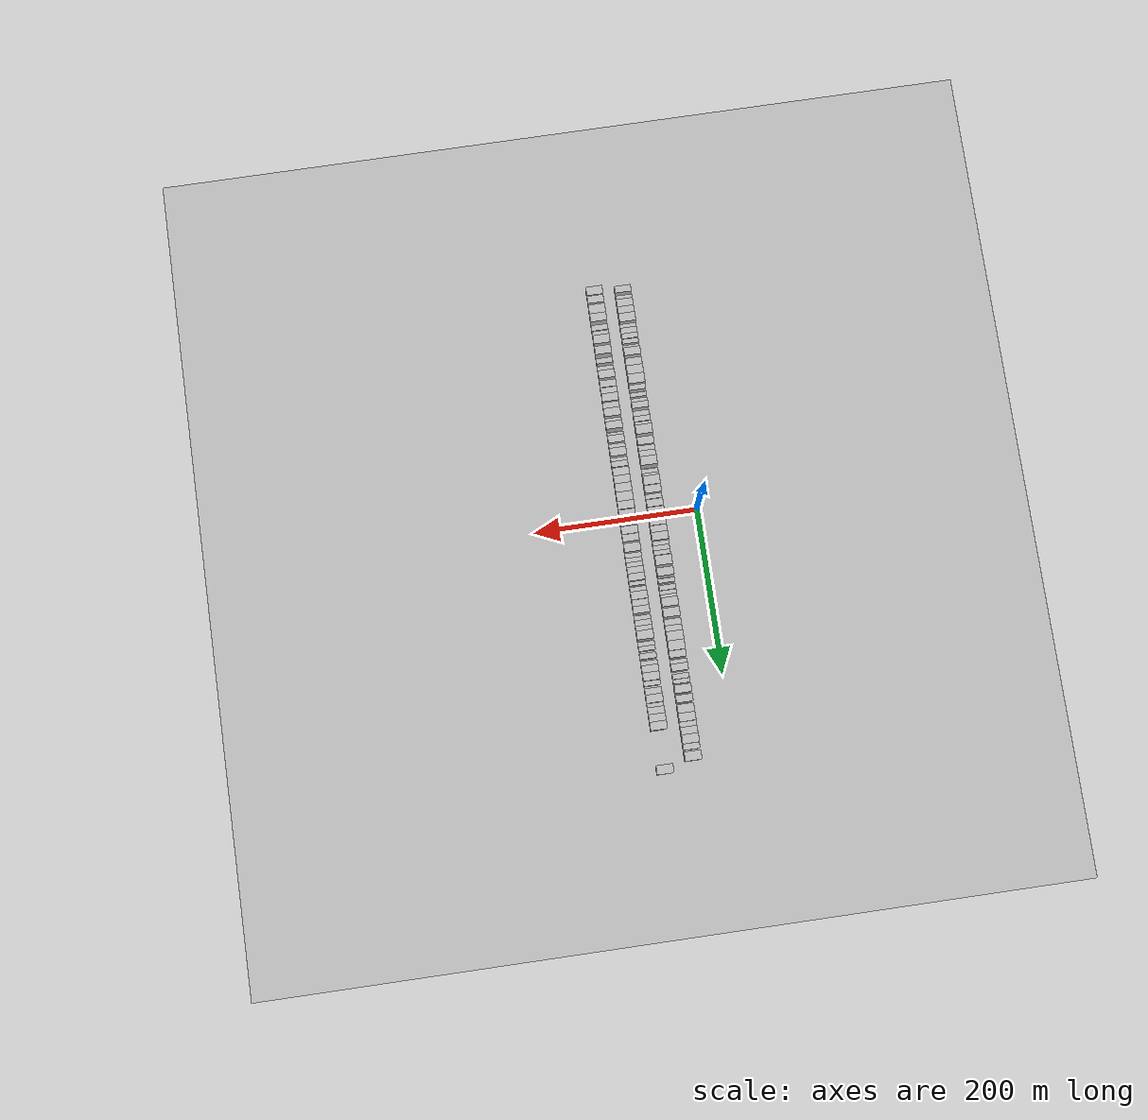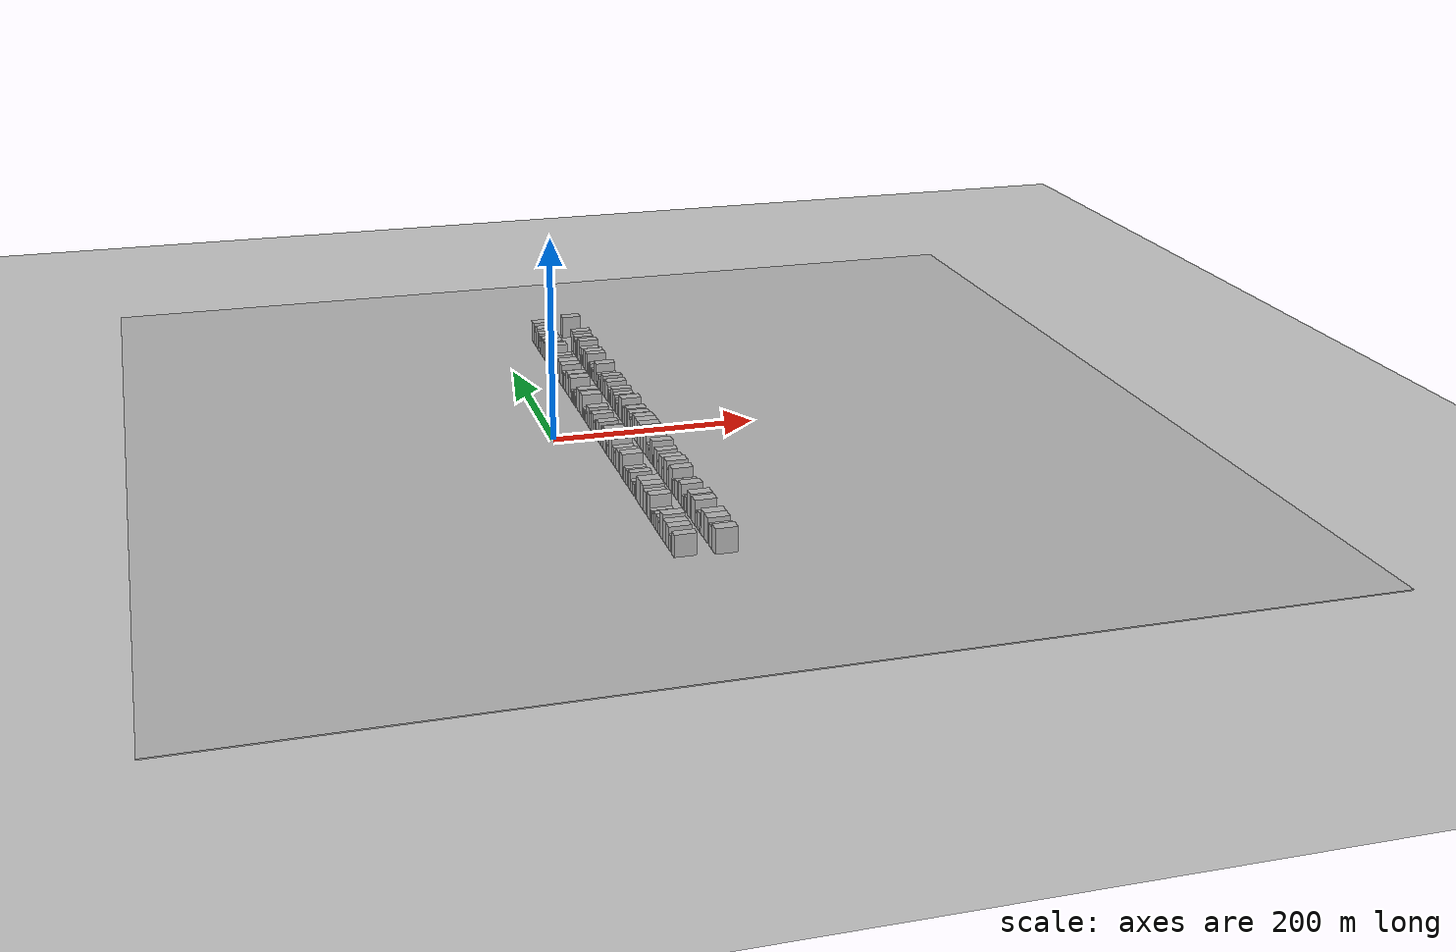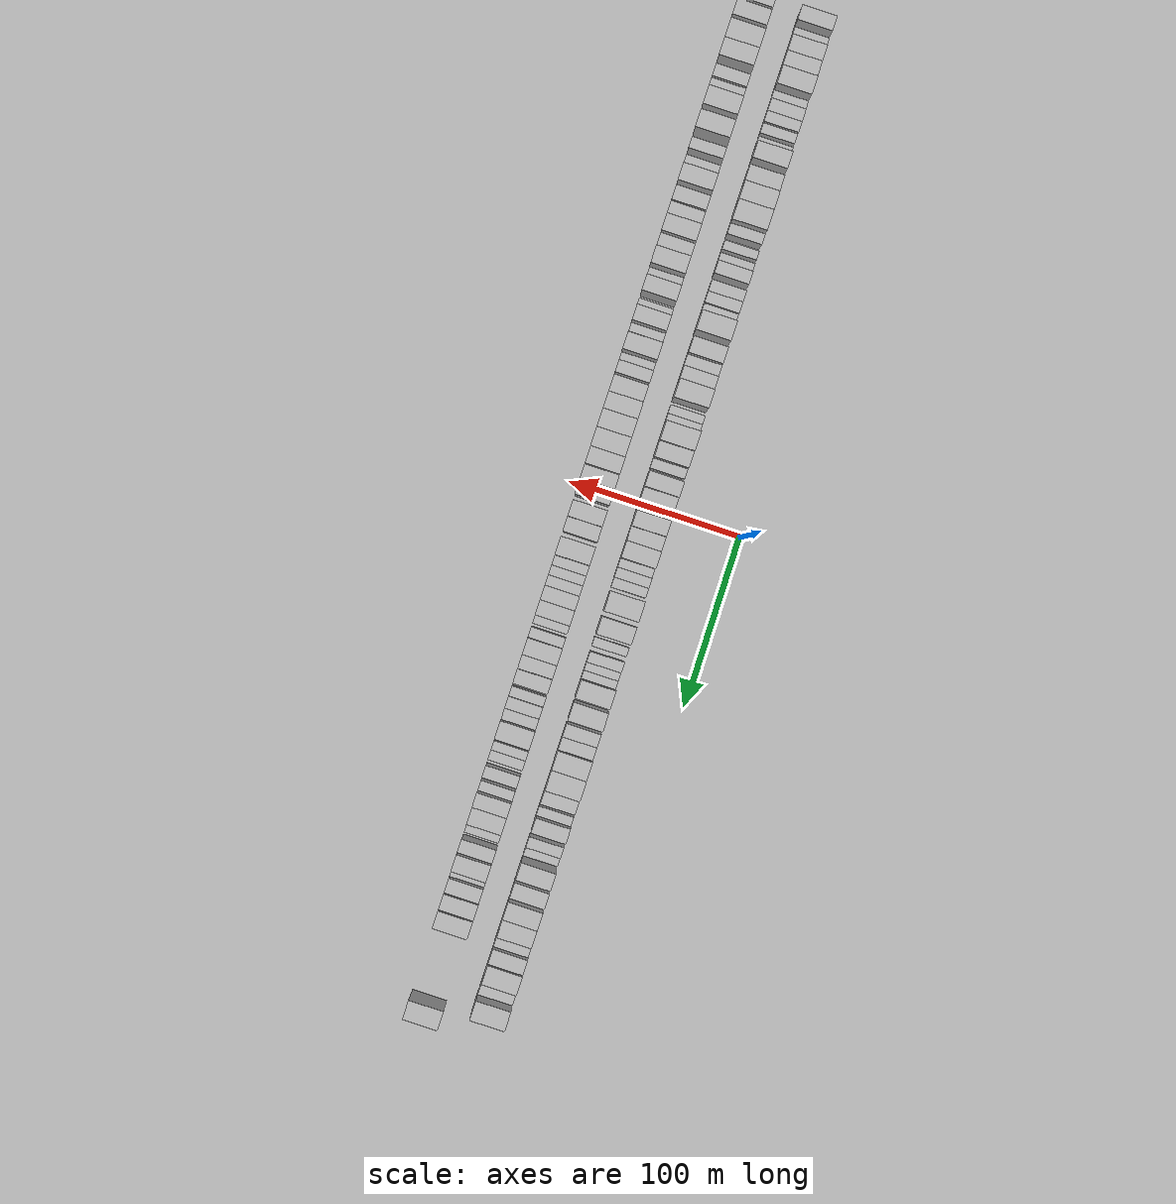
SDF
<?xml version="1.0" encoding="utf-8"?>

<sdf version="1.6">

   <world name="default">

      <gui fullscreen="0">

         <camera name="user_camera">

            <pose>-15 0 4.57585 0 0 0</pose>

            <view_controller>orbit</view_controller>

         </camera>

      </gui>

      <scene>

         <sky>

           <clouds>

             <speed>12</speed>

           </clouds>

         </sky>

         <ambient>0.4 0.4 0.4 1</ambient>

         <background>0.7 0.7 0.7 1</background>

         <shadows>1</shadows>

      </scene>

      <gravity>0 0 -9.8066</gravity>

      <magnetic_field>6e-06 2.3e-05 -4.2e-05</magnetic_field>

      <physics default="0" name="default_physics" type="ode">

         <ode>

            <solver>

               <type>quick</type>

               <iters>10</iters>

               <sor>1.0</sor>

               <use_dynamic_moi_rescaling>0</use_dynamic_moi_rescaling>

            </solver>

            <constraints>

               <cfm>0</cfm>

               <erp>0.2</erp>

               <contact_max_correcting_vel>100</contact_max_correcting_vel>

               <contact_surface_layer>0.001</contact_surface_layer>

            </constraints>

         </ode>

         <max_step_size>0.004</max_step_size>

         <real_time_factor>1</real_time_factor>

         <real_time_update_rate>250</real_time_update_rate>

      </physics>

      <light name="sun" type="directional">

         <cast_shadows>1</cast_shadows>

         <pose>0 0 10 0 0 0</pose>

         <diffuse>0.8 0.8 0.8 1</diffuse>

         <specular>0.2 0.2 0.2 1</specular>

         <attenuation>

            <range>1000</range>

            <constant>0.9</constant>

            <linear>0.01</linear>

            <quadratic>0.001</quadratic>

         </attenuation>

         <direction>-0.5 0.1 -0.9</direction>

      </light>

      <include>

         <name>ground_plane_1</name>

         <uri>model://HANNAS_ground_plane</uri>

         <pose>0 0 0  0 0 0</pose>

      </include>

      <include>

         <name>ground_plane_2</name>

         <uri>model://HANNAS_ground_plane</uri>

         <pose>100 0 0  0 0 0</pose>

      </include>

      <model name="building_1">

         <static>1</static>

         <pose frame="">50.0000 -282.7054 0 0.000000 0.000000 0.000000</pose>

         <link name="link">

            <pose frame="">0 0 10.50 0 0 0</pose>

            <collision name="collision">

               <geometry>

                  <box>

                     <size>20.0000 8.5893 21.0000</size>

                  </box>

               </geometry>

               <max_contacts>10</max_contacts>

               <surface>

                  <contact>

                     <ode/>

                  </contact>

                  <bounce/>

                  <friction>

                     <torsional>

                        <ode/>

                     </torsional>

                     <ode/>

                  </friction>

               </surface>

            </collision>

            <visual name="visual">

               <cast_shadows>0</cast_shadows>

               <geometry>

                  <box>

                     <size>20.0000 8.5893 21.0000</size>

                  </box>

               </geometry>

               <material>

                  <script>

                     <uri>model://HANNAS_wall/materials/scripts</uri>

                     <uri>model://HANNAS_wall/materials/textures</uri>

                     <name>vrc/HANNAS_wall</name>

                  </script>

               </material>

            </visual>

            <self_collide>0</self_collide>

            <enable_wind>0</enable_wind>

            <kinematic>0</kinematic>

         </link>

      </model>

      <model name="building_2">

         <static>1</static>

         <pose frame="">50.0000 -273.3137 0 0.000000 0.000000 0.000000</pose>

         <link name="link">

            <pose frame="">0 0 7.50 0 0 0</pose>

            <collision name="collision">

               <geometry>

                  <box>

                     <size>20.0000 6.1940 15.0000</size>

                  </box>

               </geometry>

               <max_contacts>10</max_contacts>

               <surface>

                  <contact>

                     <ode/>

                  </contact>

                  <bounce/>

                  <friction>

                     <torsional>

                        <ode/>

                     </torsional>

                     <ode/>

                  </friction>

               </surface>

            </collision>

            <visual name="visual">

               <cast_shadows>0</cast_shadows>

               <geometry>

                  <box>

                     <size>20.0000 6.1940 15.0000</size>

                  </box>

               </geometry>

               <material>

                  <script>

                     <uri>model://HANNAS_wall/materials/scripts</uri>

                     <uri>model://HANNAS_wall/materials/textures</uri>

                     <name>vrc/HANNAS_wall</name>

                  </script>

               </material>

            </visual>

            <self_collide>0</self_collide>

            <enable_wind>0</enable_wind>

            <kinematic>0</kinematic>

         </link>

      </model>

      <model name="building_3">

         <static>1</static>

         <pose frame="">50.0000 -265.5735 0 0.000000 0.000000 0.000000</pose>

         <link name="link">

            <pose frame="">0 0 10.50 0 0 0</pose>

            <collision name="collision">

               <geometry>

                  <box>

                     <size>20.0000 9.2864 21.0000</size>

                  </box>

               </geometry>

               <max_contacts>10</max_contacts>

               <surface>

                  <contact>

                     <ode/>

                  </contact>

                  <bounce/>

                  <friction>

                     <torsional>

                        <ode/>

                     </torsional>

                     <ode/>

                  </friction>

               </surface>

            </collision>

            <visual name="visual">

               <cast_shadows>0</cast_shadows>

               <geometry>

                  <box>

                     <size>20.0000 9.2864 21.0000</size>

                  </box>

               </geometry>

               <material>

                  <script>

                     <uri>model://HANNAS_wall/materials/scripts</uri>

                     <uri>model://HANNAS_wall/materials/textures</uri>

                     <name>vrc/HANNAS_wall</name>

                  </script>

               </material>

            </visual>

            <self_collide>0</self_collide>

            <enable_wind>0</enable_wind>

            <kinematic>0</kinematic>

         </link>

      </model>

      <model name="building_4">

         <static>1</static>

         <pose frame="">50.0000 -256.1749 0 0.000000 0.000000 0.000000</pose>

         <link name="link">

            <pose frame="">0 0 10.50 0 0 0</pose>

            <collision name="collision">

               <geometry>

                  <box>

                     <size>20.0000 9.5108 21.0000</size>

                  </box>

               </geometry>

               <max_contacts>10</max_contacts>

               <surface>

                  <contact>

                     <ode/>

                  </contact>

                  <bounce/>

                  <friction>

                     <torsional>

                        <ode/>

                     </torsional>

                     <ode/>

                  </friction>

               </surface>

            </collision>

            <visual name="visual">

               <cast_shadows>0</cast_shadows>

               <geometry>

                  <box>

                     <size>20.0000 9.5108 21.0000</size>

                  </box>

               </geometry>

               <material>

                  <script>

                     <uri>model://HANNAS_wall/materials/scripts</uri>

                     <uri>model://HANNAS_wall/materials/textures</uri>

                     <name>vrc/HANNAS_wall</name>

                  </script>

               </material>

            </visual>

            <self_collide>0</self_collide>

            <enable_wind>0</enable_wind>

            <kinematic>0</kinematic>

         </link>

      </model>

      <model name="building_5">

         <static>1</static>

         <pose frame="">50.0000 -246.0718 0 0.000000 0.000000 0.000000</pose>

         <link name="link">

            <pose frame="">0 0 12.00 0 0 0</pose>

            <collision name="collision">

               <geometry>

                  <box>

                     <size>20.0000 10.6954 24.0000</size>

                  </box>

               </geometry>

               <max_contacts>10</max_contacts>

               <surface>

                  <contact>

                     <ode/>

                  </contact>

                  <bounce/>

                  <friction>

                     <torsional>

                        <ode/>

                     </torsional>

                     <ode/>

                  </friction>

               </surface>

            </collision>

            <visual name="visual">

               <cast_shadows>0</cast_shadows>

               <geometry>

                  <box>

                     <size>20.0000 10.6954 24.0000</size>

                  </box>

               </geometry>

               <material>

                  <script>

                     <uri>model://HANNAS_wall/materials/scripts</uri>

                     <uri>model://HANNAS_wall/materials/textures</uri>

                     <name>vrc/HANNAS_wall</name>

                  </script>

               </material>

            </visual>

            <self_collide>0</self_collide>

            <enable_wind>0</enable_wind>

            <kinematic>0</kinematic>

         </link>

      </model>

      <model name="building_6">

         <static>1</static>

         <pose frame="">50.0000 -237.9298 0 0.000000 0.000000 0.000000</pose>

         <link name="link">

            <pose frame="">0 0 6.00 0 0 0</pose>

            <collision name="collision">

               <geometry>

                  <box>

                     <size>20.0000 5.5887 12.0000</size>

                  </box>

               </geometry>

               <max_contacts>10</max_contacts>

               <surface>

                  <contact>

                     <ode/>

                  </contact>

                  <bounce/>

                  <friction>

                     <torsional>

                        <ode/>

                     </torsional>

                     <ode/>

                  </friction>

               </surface>

            </collision>

            <visual name="visual">

               <cast_shadows>0</cast_shadows>

               <geometry>

                  <box>

                     <size>20.0000 5.5887 12.0000</size>

                  </box>

               </geometry>

               <material>

                  <script>

                     <uri>model://HANNAS_wall/materials/scripts</uri>

                     <uri>model://HANNAS_wall/materials/textures</uri>

                     <name>vrc/HANNAS_wall</name>

                  </script>

               </material>

            </visual>

            <self_collide>0</self_collide>

            <enable_wind>0</enable_wind>

            <kinematic>0</kinematic>

         </link>

      </model>

      <model name="building_7">

         <static>1</static>

         <pose frame="">50.0000 -231.5289 0 0.000000 0.000000 0.000000</pose>

         <link name="link">

            <pose frame="">0 0 7.50 0 0 0</pose>

            <collision name="collision">

               <geometry>

                  <box>

                     <size>20.0000 7.2132 15.0000</size>

                  </box>

               </geometry>

               <max_contacts>10</max_contacts>

               <surface>

                  <contact>

                     <ode/>

                  </contact>

                  <bounce/>

                  <friction>

                     <torsional>

                        <ode/>

                     </torsional>

                     <ode/>

                  </friction>

               </surface>

            </collision>

            <visual name="visual">

               <cast_shadows>0</cast_shadows>

               <geometry>

                  <box>

                     <size>20.0000 7.2132 15.0000</size>

                  </box>

               </geometry>

               <material>

                  <script>

                     <uri>model://HANNAS_wall/materials/scripts</uri>

                     <uri>model://HANNAS_wall/materials/textures</uri>

                     <name>vrc/HANNAS_wall</name>

                  </script>

               </material>

            </visual>

            <self_collide>0</self_collide>

            <enable_wind>0</enable_wind>

            <kinematic>0</kinematic>

         </link>

      </model>

      <model name="building_8">

         <static>1</static>

         <pose frame="">50.0000 -224.7328 0 0.000000 0.000000 0.000000</pose>

         <link name="link">

            <pose frame="">0 0 7.50 0 0 0</pose>

            <collision name="collision">

               <geometry>

                  <box>

                     <size>20.0000 6.3789 15.0000</size>

                  </box>

               </geometry>

               <max_contacts>10</max_contacts>

               <surface>

                  <contact>

                     <ode/>

                  </contact>

                  <bounce/>

                  <friction>

                     <torsional>

                        <ode/>

                     </torsional>

                     <ode/>

                  </friction>

               </surface>

            </collision>

            <visual name="visual">

               <cast_shadows>0</cast_shadows>

               <geometry>

                  <box>

                     <size>20.0000 6.3789 15.0000</size>

                  </box>

               </geometry>

               <material>

                  <script>

                     <uri>model://HANNAS_wall/materials/scripts</uri>

                     <uri>model://HANNAS_wall/materials/textures</uri>

                     <name>vrc/HANNAS_wall</name>

                  </script>

               </material>

            </visual>

            <self_collide>0</self_collide>

            <enable_wind>0</enable_wind>

            <kinematic>0</kinematic>

         </link>

      </model>

      <model name="building_9">

         <static>1</static>

         <pose frame="">50.0000 -218.6347 0 0.000000 0.000000 0.000000</pose>

         <link name="link">

            <pose frame="">0 0 6.00 0 0 0</pose>

            <collision name="collision">

               <geometry>

                  <box>

                     <size>20.0000 5.8174 12.0000</size>

                  </box>

               </geometry>

               <max_contacts>10</max_contacts>

               <surface>

                  <contact>

                     <ode/>

                  </contact>

                  <bounce/>

                  <friction>

                     <torsional>

                        <ode/>

                     </torsional>

                     <ode/>

                  </friction>

               </surface>

            </collision>

            <visual name="visual">

               <cast_shadows>0</cast_shadows>

               <geometry>

                  <box>

                     <size>20.0000 5.8174 12.0000</size>

                  </box>

               </geometry>

               <material>

                  <script>

                     <uri>model://HANNAS_wall/materials/scripts</uri>

                     <uri>model://HANNAS_wall/materials/textures</uri>

                     <name>vrc/HANNAS_wall</name>

                  </script>

               </material>

            </visual>

            <self_collide>0</self_collide>

            <enable_wind>0</enable_wind>

            <kinematic>0</kinematic>

         </link>

      </model>

      <model name="building_10">

         <static>1</static>

         <pose frame="">50.0000 -210.8293 0 0.000000 0.000000 0.000000</pose>

         <link name="link">

            <pose frame="">0 0 6.00 0 0 0</pose>

            <collision name="collision">

               <geometry>

                  <box>

                     <size>20.0000 5.7934 12.0000</size>

                  </box>

               </geometry>

               <max_contacts>10</max_contacts>

               <surface>

                  <contact>

                     <ode/>

                  </contact>

                  <bounce/>

                  <friction>

                     <torsional>

                        <ode/>

                     </torsional>

                     <ode/>

                  </friction>

               </surface>

            </collision>

            <visual name="visual">

               <cast_shadows>0</cast_shadows>

               <geometry>

                  <box>

                     <size>20.0000 5.7934 12.0000</size>

                  </box>

               </geometry>

               <material>

                  <script>

                     <uri>model://HANNAS_wall/materials/scripts</uri>

                     <uri>model://HANNAS_wall/materials/textures</uri>

                     <name>vrc/HANNAS_wall</name>

                  </script>

               </material>

            </visual>

            <self_collide>0</self_collide>

            <enable_wind>0</enable_wind>

            <kinematic>0</kinematic>

         </link>

      </model>

      <model name="building_11">

         <static>1</static>

         <pose frame="">50.0000 -202.9933 0 0.000000 0.000000 0.000000</pose>

         <link name="link">

            <pose frame="">0 0 12.00 0 0 0</pose>

            <collision name="collision">

               <geometry>

                  <box>

                     <size>20.0000 9.8786 24.0000</size>

                  </box>

               </geometry>

               <max_contacts>10</max_contacts>

               <surface>

                  <contact>

                     <ode/>

                  </contact>

                  <bounce/>

                  <friction>

                     <torsional>

                        <ode/>

                     </torsional>

                     <ode/>

                  </friction>

               </surface>

            </collision>

            <visual name="visual">

               <cast_shadows>0</cast_shadows>

               <geometry>

                  <box>

                     <size>20.0000 9.8786 24.0000</size>

                  </box>

               </geometry>

               <material>

                  <script>

                     <uri>model://HANNAS_wall/materials/scripts</uri>

                     <uri>model://HANNAS_wall/materials/textures</uri>

                     <name>vrc/HANNAS_wall</name>

                  </script>

               </material>

            </visual>

            <self_collide>0</self_collide>

            <enable_wind>0</enable_wind>

            <kinematic>0</kinematic>

         </link>

      </model>

      <model name="building_12">

         <static>1</static>

         <pose frame="">50.0000 -190.0922 0 0.000000 0.000000 0.000000</pose>

         <link name="link">

            <pose frame="">0 0 10.50 0 0 0</pose>

            <collision name="collision">

               <geometry>

                  <box>

                     <size>20.0000 9.9234 21.0000</size>

                  </box>

               </geometry>

               <max_contacts>10</max_contacts>

               <surface>

                  <contact>

                     <ode/>

                  </contact>

                  <bounce/>

                  <friction>

                     <torsional>

                        <ode/>

                     </torsional>

                     <ode/>

                  </friction>

               </surface>

            </collision>

            <visual name="visual">

               <cast_shadows>0</cast_shadows>

               <geometry>

                  <box>

                     <size>20.0000 9.9234 21.0000</size>

                  </box>

               </geometry>

               <material>

                  <script>

                     <uri>model://HANNAS_wall/materials/scripts</uri>

                     <uri>model://HANNAS_wall/materials/textures</uri>

                     <name>vrc/HANNAS_wall</name>

                  </script>

               </material>

            </visual>

            <self_collide>0</self_collide>

            <enable_wind>0</enable_wind>

            <kinematic>0</kinematic>

         </link>

      </model>

      <model name="building_13">

         <static>1</static>

         <pose frame="">50.0000 -179.8102 0 0.000000 0.000000 0.000000</pose>

         <link name="link">

            <pose frame="">0 0 12.00 0 0 0</pose>

            <collision name="collision">

               <geometry>

                  <box>

                     <size>20.0000 10.6407 24.0000</size>

                  </box>

               </geometry>

               <max_contacts>10</max_contacts>

               <surface>

                  <contact>

                     <ode/>

                  </contact>

                  <bounce/>

                  <friction>

                     <torsional>

                        <ode/>

                     </torsional>

                     <ode/>

                  </friction>

               </surface>

            </collision>

            <visual name="visual">

               <cast_shadows>0</cast_shadows>

               <geometry>

                  <box>

                     <size>20.0000 10.6407 24.0000</size>

                  </box>

               </geometry>

               <material>

                  <script>

                     <uri>model://HANNAS_wall/materials/scripts</uri>

                     <uri>model://HANNAS_wall/materials/textures</uri>

                     <name>vrc/HANNAS_wall</name>

                  </script>

               </material>

            </visual>

            <self_collide>0</self_collide>

            <enable_wind>0</enable_wind>

            <kinematic>0</kinematic>

         </link>

      </model>

      <model name="building_14">

         <static>1</static>

         <pose frame="">50.0000 -168.5287 0 0.000000 0.000000 0.000000</pose>

         <link name="link">

            <pose frame="">0 0 12.00 0 0 0</pose>

            <collision name="collision">

               <geometry>

                  <box>

                     <size>20.0000 11.9223 24.0000</size>

                  </box>

               </geometry>

               <max_contacts>10</max_contacts>

               <surface>

                  <contact>

                     <ode/>

                  </contact>

                  <bounce/>

                  <friction>

                     <torsional>

                        <ode/>

                     </torsional>

                     <ode/>

                  </friction>

               </surface>

            </collision>

            <visual name="visual">

               <cast_shadows>0</cast_shadows>

               <geometry>

                  <box>

                     <size>20.0000 11.9223 24.0000</size>

                  </box>

               </geometry>

               <material>

                  <script>

                     <uri>model://HANNAS_wall/materials/scripts</uri>

                     <uri>model://HANNAS_wall/materials/textures</uri>

                     <name>vrc/HANNAS_wall</name>

                  </script>

               </material>

            </visual>

            <self_collide>0</self_collide>

            <enable_wind>0</enable_wind>

            <kinematic>0</kinematic>

         </link>

      </model>

      <model name="building_15">

         <static>1</static>

         <pose frame="">50.0000 -159.4381 0 0.000000 0.000000 0.000000</pose>

         <link name="link">

            <pose frame="">0 0 7.50 0 0 0</pose>

            <collision name="collision">

               <geometry>

                  <box>

                     <size>20.0000 6.2589 15.0000</size>

                  </box>

               </geometry>

               <max_contacts>10</max_contacts>

               <surface>

                  <contact>

                     <ode/>

                  </contact>

                  <bounce/>

                  <friction>

                     <torsional>

                        <ode/>

                     </torsional>

                     <ode/>

                  </friction>

               </surface>

            </collision>

            <visual name="visual">

               <cast_shadows>0</cast_shadows>

               <geometry>

                  <box>

                     <size>20.0000 6.2589 15.0000</size>

                  </box>

               </geometry>

               <material>

                  <script>

                     <uri>model://HANNAS_wall/materials/scripts</uri>

                     <uri>model://HANNAS_wall/materials/textures</uri>

                     <name>vrc/HANNAS_wall</name>

                  </script>

               </material>

            </visual>

            <self_collide>0</self_collide>

            <enable_wind>0</enable_wind>

            <kinematic>0</kinematic>

         </link>

      </model>

      <model name="building_16">

         <static>1</static>

         <pose frame="">50.0000 -150.6454 0 0.000000 0.000000 0.000000</pose>

         <link name="link">

            <pose frame="">0 0 6.00 0 0 0</pose>

            <collision name="collision">

               <geometry>

                  <box>

                     <size>20.0000 5.3266 12.0000</size>

                  </box>

               </geometry>

               <max_contacts>10</max_contacts>

               <surface>

                  <contact>

                     <ode/>

                  </contact>

                  <bounce/>

                  <friction>

                     <torsional>

                        <ode/>

                     </torsional>

                     <ode/>

                  </friction>

               </surface>

            </collision>

            <visual name="visual">

               <cast_shadows>0</cast_shadows>

               <geometry>

                  <box>

                     <size>20.0000 5.3266 12.0000</size>

                  </box>

               </geometry>

               <material>

                  <script>

                     <uri>model://HANNAS_wall/materials/scripts</uri>

                     <uri>model://HANNAS_wall/materials/textures</uri>

                     <name>vrc/HANNAS_wall</name>

                  </script>

               </material>

            </visual>

            <self_collide>0</self_collide>

            <enable_wind>0</enable_wind>

            <kinematic>0</kinematic>

         </link>

      </model>

      <model name="building_17">

         <static>1</static>

         <pose frame="">50.0000 -143.1779 0 0.000000 0.000000 0.000000</pose>

         <link name="link">

            <pose frame="">0 0 6.00 0 0 0</pose>

            <collision name="collision">

               <geometry>

                  <box>

                     <size>20.0000 5.6084 12.0000</size>

                  </box>

               </geometry>

               <max_contacts>10</max_contacts>

               <surface>

                  <contact>

                     <ode/>

                  </contact>

                  <bounce/>

                  <friction>

                     <torsional>

                        <ode/>

                     </torsional>

                     <ode/>

                  </friction>

               </surface>

            </collision>

            <visual name="visual">

               <cast_shadows>0</cast_shadows>

               <geometry>

                  <box>

                     <size>20.0000 5.6084 12.0000</size>

                  </box>

               </geometry>

               <material>

                  <script>

                     <uri>model://HANNAS_wall/materials/scripts</uri>

                     <uri>model://HANNAS_wall/materials/textures</uri>

                     <name>vrc/HANNAS_wall</name>

                  </script>

               </material>

            </visual>

            <self_collide>0</self_collide>

            <enable_wind>0</enable_wind>

            <kinematic>0</kinematic>

         </link>

      </model>

      <model name="building_18">

         <static>1</static>

         <pose frame="">50.0000 -136.5810 0 0.000000 0.000000 0.000000</pose>

         <link name="link">

            <pose frame="">0 0 9.00 0 0 0</pose>

            <collision name="collision">

               <geometry>

                  <box>

                     <size>20.0000 7.5854 18.0000</size>

                  </box>

               </geometry>

               <max_contacts>10</max_contacts>

               <surface>

                  <contact>

                     <ode/>

                  </contact>

                  <bounce/>

                  <friction>

                     <torsional>

                        <ode/>

                     </torsional>

                     <ode/>

                  </friction>

               </surface>

            </collision>

            <visual name="visual">

               <cast_shadows>0</cast_shadows>

               <geometry>

                  <box>

                     <size>20.0000 7.5854 18.0000</size>

                  </box>

               </geometry>

               <material>

                  <script>

                     <uri>model://HANNAS_wall/materials/scripts</uri>

                     <uri>model://HANNAS_wall/materials/textures</uri>

                     <name>vrc/HANNAS_wall</name>

                  </script>

               </material>

            </visual>

            <self_collide>0</self_collide>

            <enable_wind>0</enable_wind>

            <kinematic>0</kinematic>

         </link>

      </model>

      <model name="building_19">

         <static>1</static>

         <pose frame="">50.0000 -126.4418 0 0.000000 0.000000 0.000000</pose>

         <link name="link">

            <pose frame="">0 0 7.50 0 0 0</pose>

            <collision name="collision">

               <geometry>

                  <box>

                     <size>20.0000 6.6930 15.0000</size>

                  </box>

               </geometry>

               <max_contacts>10</max_contacts>

               <surface>

                  <contact>

                     <ode/>

                  </contact>

                  <bounce/>

                  <friction>

                     <torsional>

                        <ode/>

                     </torsional>

                     <ode/>

                  </friction>

               </surface>

            </collision>

            <visual name="visual">

               <cast_shadows>0</cast_shadows>

               <geometry>

                  <box>

                     <size>20.0000 6.6930 15.0000</size>

                  </box>

               </geometry>

               <material>

                  <script>

                     <uri>model://HANNAS_wall/materials/scripts</uri>

                     <uri>model://HANNAS_wall/materials/textures</uri>

                     <name>vrc/HANNAS_wall</name>

                  </script>

               </material>

            </visual>

            <self_collide>0</self_collide>

            <enable_wind>0</enable_wind>

            <kinematic>0</kinematic>

         </link>

      </model>

      <model name="building_20">

         <static>1</static>

         <pose frame="">50.0000 -119.7794 0 0.000000 0.000000 0.000000</pose>

         <link name="link">

            <pose frame="">0 0 7.50 0 0 0</pose>

            <collision name="collision">

               <geometry>

                  <box>

                     <size>20.0000 6.6319 15.0000</size>

                  </box>

               </geometry>

               <max_contacts>10</max_contacts>

               <surface>

                  <contact>

                     <ode/>

                  </contact>

                  <bounce/>

                  <friction>

                     <torsional>

                        <ode/>

                     </torsional>

                     <ode/>

                  </friction>

               </surface>

            </collision>

            <visual name="visual">

               <cast_shadows>0</cast_shadows>

               <geometry>

                  <box>

                     <size>20.0000 6.6319 15.0000</size>

                  </box>

               </geometry>

               <material>

                  <script>

                     <uri>model://HANNAS_wall/materials/scripts</uri>

                     <uri>model://HANNAS_wall/materials/textures</uri>

                     <name>vrc/HANNAS_wall</name>

                  </script>

               </material>

            </visual>

            <self_collide>0</self_collide>

            <enable_wind>0</enable_wind>

            <kinematic>0</kinematic>

         </link>

      </model>

      <model name="building_21">

         <static>1</static>

         <pose frame="">50.0000 -113.5627 0 0.000000 0.000000 0.000000</pose>

         <link name="link">

            <pose frame="">0 0 6.00 0 0 0</pose>

            <collision name="collision">

               <geometry>

                  <box>

                     <size>20.0000 5.8016 12.0000</size>

                  </box>

               </geometry>

               <max_contacts>10</max_contacts>

               <surface>

                  <contact>

                     <ode/>

                  </contact>

                  <bounce/>

                  <friction>

                     <torsional>

                        <ode/>

                     </torsional>

                     <ode/>

                  </friction>

               </surface>

            </collision>

            <visual name="visual">

               <cast_shadows>0</cast_shadows>

               <geometry>

                  <box>

                     <size>20.0000 5.8016 12.0000</size>

                  </box>

               </geometry>

               <material>

                  <script>

                     <uri>model://HANNAS_wall/materials/scripts</uri>

                     <uri>model://HANNAS_wall/materials/textures</uri>

                     <name>vrc/HANNAS_wall</name>

                  </script>

               </material>

            </visual>

            <self_collide>0</self_collide>

            <enable_wind>0</enable_wind>

            <kinematic>0</kinematic>

         </link>

      </model>

      <model name="building_22">

         <static>1</static>

         <pose frame="">50.0000 -104.8681 0 0.000000 0.000000 0.000000</pose>

         <link name="link">

            <pose frame="">0 0 12.00 0 0 0</pose>

            <collision name="collision">

               <geometry>

                  <box>

                     <size>20.0000 11.5875 24.0000</size>

                  </box>

               </geometry>

               <max_contacts>10</max_contacts>

               <surface>

                  <contact>

                     <ode/>

                  </contact>

                  <bounce/>

                  <friction>

                     <torsional>

                        <ode/>

                     </torsional>

                     <ode/>

                  </friction>

               </surface>

            </collision>

            <visual name="visual">

               <cast_shadows>0</cast_shadows>

               <geometry>

                  <box>

                     <size>20.0000 11.5875 24.0000</size>

                  </box>

               </geometry>

               <material>

                  <script>

                     <uri>model://HANNAS_wall/materials/scripts</uri>

                     <uri>model://HANNAS_wall/materials/textures</uri>

                     <name>vrc/HANNAS_wall</name>

                  </script>

               </material>

            </visual>

            <self_collide>0</self_collide>

            <enable_wind>0</enable_wind>

            <kinematic>0</kinematic>

         </link>

      </model>

      <model name="building_23">

         <static>1</static>

         <pose frame="">50.0000 -91.2402 0 0.000000 0.000000 0.000000</pose>

         <link name="link">

            <pose frame="">0 0 10.50 0 0 0</pose>

            <collision name="collision">

               <geometry>

                  <box>

                     <size>20.0000 9.6684 21.0000</size>

                  </box>

               </geometry>

               <max_contacts>10</max_contacts>

               <surface>

                  <contact>

                     <ode/>

                  </contact>

                  <bounce/>

                  <friction>

                     <torsional>

                        <ode/>

                     </torsional>

                     <ode/>

                  </friction>

               </surface>

            </collision>

            <visual name="visual">

               <cast_shadows>0</cast_shadows>

               <geometry>

                  <box>

                     <size>20.0000 9.6684 21.0000</size>

                  </box>

               </geometry>

               <material>

                  <script>

                     <uri>model://HANNAS_wall/materials/scripts</uri>

                     <uri>model://HANNAS_wall/materials/textures</uri>

                     <name>vrc/HANNAS_wall</name>

                  </script>

               </material>

            </visual>

            <self_collide>0</self_collide>

            <enable_wind>0</enable_wind>

            <kinematic>0</kinematic>

         </link>

      </model>

      <model name="building_24">

         <static>1</static>

         <pose frame="">50.0000 -82.9417 0 0.000000 0.000000 0.000000</pose>

         <link name="link">

            <pose frame="">0 0 7.50 0 0 0</pose>

            <collision name="collision">

               <geometry>

                  <box>

                     <size>20.0000 6.9285 15.0000</size>

                  </box>

               </geometry>

               <max_contacts>10</max_contacts>

               <surface>

                  <contact>

                     <ode/>

                  </contact>

                  <bounce/>

                  <friction>

                     <torsional>

                        <ode/>

                     </torsional>

                     <ode/>

                  </friction>

               </surface>

            </collision>

            <visual name="visual">

               <cast_shadows>0</cast_shadows>

               <geometry>

                  <box>

                     <size>20.0000 6.9285 15.0000</size>

                  </box>

               </geometry>

               <material>

                  <script>

                     <uri>model://HANNAS_wall/materials/scripts</uri>

                     <uri>model://HANNAS_wall/materials/textures</uri>

                     <name>vrc/HANNAS_wall</name>

                  </script>

               </material>

            </visual>

            <self_collide>0</self_collide>

            <enable_wind>0</enable_wind>

            <kinematic>0</kinematic>

         </link>

      </model>

      <model name="building_25">

         <static>1</static>

         <pose frame="">50.0000 -75.3658 0 0.000000 0.000000 0.000000</pose>

         <link name="link">

            <pose frame="">0 0 9.00 0 0 0</pose>

            <collision name="collision">

               <geometry>

                  <box>

                     <size>20.0000 8.2234 18.0000</size>

                  </box>

               </geometry>

               <max_contacts>10</max_contacts>

               <surface>

                  <contact>

                     <ode/>

                  </contact>

                  <bounce/>

                  <friction>

                     <torsional>

                        <ode/>

                     </torsional>

                     <ode/>

                  </friction>

               </surface>

            </collision>

            <visual name="visual">

               <cast_shadows>0</cast_shadows>

               <geometry>

                  <box>

                     <size>20.0000 8.2234 18.0000</size>

                  </box>

               </geometry>

               <material>

                  <script>

                     <uri>model://HANNAS_wall/materials/scripts</uri>

                     <uri>model://HANNAS_wall/materials/textures</uri>

                     <name>vrc/HANNAS_wall</name>

                  </script>

               </material>

            </visual>

            <self_collide>0</self_collide>

            <enable_wind>0</enable_wind>

            <kinematic>0</kinematic>

         </link>

      </model>

      <model name="building_26">

         <static>1</static>

         <pose frame="">50.0000 -65.8035 0 0.000000 0.000000 0.000000</pose>

         <link name="link">

            <pose frame="">0 0 12.00 0 0 0</pose>

            <collision name="collision">

               <geometry>

                  <box>

                     <size>20.0000 10.9014 24.0000</size>

                  </box>

               </geometry>

               <max_contacts>10</max_contacts>

               <surface>

                  <contact>

                     <ode/>

                  </contact>

                  <bounce/>

                  <friction>

                     <torsional>

                        <ode/>

                     </torsional>

                     <ode/>

                  </friction>

               </surface>

            </collision>

            <visual name="visual">

               <cast_shadows>0</cast_shadows>

               <geometry>

                  <box>

                     <size>20.0000 10.9014 24.0000</size>

                  </box>

               </geometry>

               <material>

                  <script>

                     <uri>model://HANNAS_wall/materials/scripts</uri>

                     <uri>model://HANNAS_wall/materials/textures</uri>

                     <name>vrc/HANNAS_wall</name>

                  </script>

               </material>

            </visual>

            <self_collide>0</self_collide>

            <enable_wind>0</enable_wind>

            <kinematic>0</kinematic>

         </link>

      </model>

      <model name="building_27">

         <static>1</static>

         <pose frame="">50.0000 -54.8230 0 0.000000 0.000000 0.000000</pose>

         <link name="link">

            <pose frame="">0 0 6.00 0 0 0</pose>

            <collision name="collision">

               <geometry>

                  <box>

                     <size>20.0000 5.0596 12.0000</size>

                  </box>

               </geometry>

               <max_contacts>10</max_contacts>

               <surface>

                  <contact>

                     <ode/>

                  </contact>

                  <bounce/>

                  <friction>

                     <torsional>

                        <ode/>

                     </torsional>

                     <ode/>

                  </friction>

               </surface>

            </collision>

            <visual name="visual">

               <cast_shadows>0</cast_shadows>

               <geometry>

                  <box>

                     <size>20.0000 5.0596 12.0000</size>

                  </box>

               </geometry>

               <material>

                  <script>

                     <uri>model://HANNAS_wall/materials/scripts</uri>

                     <uri>model://HANNAS_wall/materials/textures</uri>

                     <name>vrc/HANNAS_wall</name>

                  </script>

               </material>

            </visual>

            <self_collide>0</self_collide>

            <enable_wind>0</enable_wind>

            <kinematic>0</kinematic>

         </link>

      </model>

      <model name="building_28">

         <static>1</static>

         <pose frame="">50.0000 -49.7295 0 0.000000 0.000000 0.000000</pose>

         <link name="link">

            <pose frame="">0 0 6.00 0 0 0</pose>

            <collision name="collision">

               <geometry>

                  <box>

                     <size>20.0000 5.1273 12.0000</size>

                  </box>

               </geometry>

               <max_contacts>10</max_contacts>

               <surface>

                  <contact>

                     <ode/>

                  </contact>

                  <bounce/>

                  <friction>

                     <torsional>

                        <ode/>

                     </torsional>

                     <ode/>

                  </friction>

               </surface>

            </collision>

            <visual name="visual">

               <cast_shadows>0</cast_shadows>

               <geometry>

                  <box>

                     <size>20.0000 5.1273 12.0000</size>

                  </box>

               </geometry>

               <material>

                  <script>

                     <uri>model://HANNAS_wall/materials/scripts</uri>

                     <uri>model://HANNAS_wall/materials/textures</uri>

                     <name>vrc/HANNAS_wall</name>

                  </script>

               </material>

            </visual>

            <self_collide>0</self_collide>

            <enable_wind>0</enable_wind>

            <kinematic>0</kinematic>

         </link>

      </model>

      <model name="building_29">

         <static>1</static>

         <pose frame="">50.0000 -41.5138 0 0.000000 0.000000 0.000000</pose>

         <link name="link">

            <pose frame="">0 0 12.00 0 0 0</pose>

            <collision name="collision">

               <geometry>

                  <box>

                     <size>20.0000 11.3039 24.0000</size>

                  </box>

               </geometry>

               <max_contacts>10</max_contacts>

               <surface>

                  <contact>

                     <ode/>

                  </contact>

                  <bounce/>

                  <friction>

                     <torsional>

                        <ode/>

                     </torsional>

                     <ode/>

                  </friction>

               </surface>

            </collision>

            <visual name="visual">

               <cast_shadows>0</cast_shadows>

               <geometry>

                  <box>

                     <size>20.0000 11.3039 24.0000</size>

                  </box>

               </geometry>

               <material>

                  <script>

                     <uri>model://HANNAS_wall/materials/scripts</uri>

                     <uri>model://HANNAS_wall/materials/textures</uri>

                     <name>vrc/HANNAS_wall</name>

                  </script>

               </material>

            </visual>

            <self_collide>0</self_collide>

            <enable_wind>0</enable_wind>

            <kinematic>0</kinematic>

         </link>

      </model>

      <model name="building_30">

         <static>1</static>

         <pose frame="">50.0000 -31.1243 0 0.000000 0.000000 0.000000</pose>

         <link name="link">

            <pose frame="">0 0 10.50 0 0 0</pose>

            <collision name="collision">

               <geometry>

                  <box>

                     <size>20.0000 9.4751 21.0000</size>

                  </box>

               </geometry>

               <max_contacts>10</max_contacts>

               <surface>

                  <contact>

                     <ode/>

                  </contact>

                  <bounce/>

                  <friction>

                     <torsional>

                        <ode/>

                     </torsional>

                     <ode/>

                  </friction>

               </surface>

            </collision>

            <visual name="visual">

               <cast_shadows>0</cast_shadows>

               <geometry>

                  <box>

                     <size>20.0000 9.4751 21.0000</size>

                  </box>

               </geometry>

               <material>

                  <script>

                     <uri>model://HANNAS_wall/materials/scripts</uri>

                     <uri>model://HANNAS_wall/materials/textures</uri>

                     <name>vrc/HANNAS_wall</name>

                  </script>

               </material>

            </visual>

            <self_collide>0</self_collide>

            <enable_wind>0</enable_wind>

            <kinematic>0</kinematic>

         </link>

      </model>

      <model name="building_31">

         <static>1</static>

         <pose frame="">50.0000 -23.4259 0 0.000000 0.000000 0.000000</pose>

         <link name="link">

            <pose frame="">0 0 6.00 0 0 0</pose>

            <collision name="collision">

               <geometry>

                  <box>

                     <size>20.0000 5.9219 12.0000</size>

                  </box>

               </geometry>

               <max_contacts>10</max_contacts>

               <surface>

                  <contact>

                     <ode/>

                  </contact>

                  <bounce/>

                  <friction>

                     <torsional>

                        <ode/>

                     </torsional>

                     <ode/>

                  </friction>

               </surface>

            </collision>

            <visual name="visual">

               <cast_shadows>0</cast_shadows>

               <geometry>

                  <box>

                     <size>20.0000 5.9219 12.0000</size>

                  </box>

               </geometry>

               <material>

                  <script>

                     <uri>model://HANNAS_wall/materials/scripts</uri>

                     <uri>model://HANNAS_wall/materials/textures</uri>

                     <name>vrc/HANNAS_wall</name>

                  </script>

               </material>

            </visual>

            <self_collide>0</self_collide>

            <enable_wind>0</enable_wind>

            <kinematic>0</kinematic>

         </link>

      </model>

      <model name="building_32">

         <static>1</static>

         <pose frame="">50.0000 -13.8963 0 0.000000 0.000000 0.000000</pose>

         <link name="link">

            <pose frame="">0 0 10.50 0 0 0</pose>

            <collision name="collision">

               <geometry>

                  <box>

                     <size>20.0000 9.1371 21.0000</size>

                  </box>

               </geometry>

               <max_contacts>10</max_contacts>

               <surface>

                  <contact>

                     <ode/>

                  </contact>

                  <bounce/>

                  <friction>

                     <torsional>

                        <ode/>

                     </torsional>

                     <ode/>

                  </friction>

               </surface>

            </collision>

            <visual name="visual">

               <cast_shadows>0</cast_shadows>

               <geometry>

                  <box>

                     <size>20.0000 9.1371 21.0000</size>

                  </box>

               </geometry>

               <material>

                  <script>

                     <uri>model://HANNAS_wall/materials/scripts</uri>

                     <uri>model://HANNAS_wall/materials/textures</uri>

                     <name>vrc/HANNAS_wall</name>

                  </script>

               </material>

            </visual>

            <self_collide>0</self_collide>

            <enable_wind>0</enable_wind>

            <kinematic>0</kinematic>

         </link>

      </model>

      <model name="building_33">

         <static>1</static>

         <pose frame="">50.0000 -5.6347 0 0.000000 0.000000 0.000000</pose>

         <link name="link">

            <pose frame="">0 0 9.00 0 0 0</pose>

            <collision name="collision">

               <geometry>

                  <box>

                     <size>20.0000 7.3862 18.0000</size>

                  </box>

               </geometry>

               <max_contacts>10</max_contacts>

               <surface>

                  <contact>

                     <ode/>

                  </contact>

                  <bounce/>

                  <friction>

                     <torsional>

                        <ode/>

                     </torsional>

                     <ode/>

                  </friction>

               </surface>

            </collision>

            <visual name="visual">

               <cast_shadows>0</cast_shadows>

               <geometry>

                  <box>

                     <size>20.0000 7.3862 18.0000</size>

                  </box>

               </geometry>

               <material>

                  <script>

                     <uri>model://HANNAS_wall/materials/scripts</uri>

                     <uri>model://HANNAS_wall/materials/textures</uri>

                     <name>vrc/HANNAS_wall</name>

                  </script>

               </material>

            </visual>

            <self_collide>0</self_collide>

            <enable_wind>0</enable_wind>

            <kinematic>0</kinematic>

         </link>

      </model>

      <model name="building_34">

         <static>1</static>

         <pose frame="">50.0000 1.0851 0 0.000000 0.000000 0.000000</pose>

         <link name="link">

            <pose frame="">0 0 7.50 0 0 0</pose>

            <collision name="collision">

               <geometry>

                  <box>

                     <size>20.0000 6.0533 15.0000</size>

                  </box>

               </geometry>

               <max_contacts>10</max_contacts>

               <surface>

                  <contact>

                     <ode/>

                  </contact>

                  <bounce/>

                  <friction>

                     <torsional>

                        <ode/>

                     </torsional>

                     <ode/>

                  </friction>

               </surface>

            </collision>

            <visual name="visual">

               <cast_shadows>0</cast_shadows>

               <geometry>

                  <box>

                     <size>20.0000 6.0533 15.0000</size>

                  </box>

               </geometry>

               <material>

                  <script>

                     <uri>model://HANNAS_wall/materials/scripts</uri>

                     <uri>model://HANNAS_wall/materials/textures</uri>

                     <name>vrc/HANNAS_wall</name>

                  </script>

               </material>

            </visual>

            <self_collide>0</self_collide>

            <enable_wind>0</enable_wind>

            <kinematic>0</kinematic>

         </link>

      </model>

      <model name="building_35">

         <static>1</static>

         <pose frame="">50.0000 8.7507 0 0.000000 0.000000 0.000000</pose>

         <link name="link">

            <pose frame="">0 0 10.50 0 0 0</pose>

            <collision name="collision">

               <geometry>

                  <box>

                     <size>20.0000 9.2780 21.0000</size>

                  </box>

               </geometry>

               <max_contacts>10</max_contacts>

               <surface>

                  <contact>

                     <ode/>

                  </contact>

                  <bounce/>

                  <friction>

                     <torsional>

                        <ode/>

                     </torsional>

                     <ode/>

                  </friction>

               </surface>

            </collision>

            <visual name="visual">

               <cast_shadows>0</cast_shadows>

               <geometry>

                  <box>

                     <size>20.0000 9.2780 21.0000</size>

                  </box>

               </geometry>

               <material>

                  <script>

                     <uri>model://HANNAS_wall/materials/scripts</uri>

                     <uri>model://HANNAS_wall/materials/textures</uri>

                     <name>vrc/HANNAS_wall</name>

                  </script>

               </material>

            </visual>

            <self_collide>0</self_collide>

            <enable_wind>0</enable_wind>

            <kinematic>0</kinematic>

         </link>

      </model>

      <model name="building_36">

         <static>1</static>

         <pose frame="">50.0000 17.6079 0 0.000000 0.000000 0.000000</pose>

         <link name="link">

            <pose frame="">0 0 9.00 0 0 0</pose>

            <collision name="collision">

               <geometry>

                  <box>

                     <size>20.0000 8.4364 18.0000</size>

                  </box>

               </geometry>

               <max_contacts>10</max_contacts>

               <surface>

                  <contact>

                     <ode/>

                  </contact>

                  <bounce/>

                  <friction>

                     <torsional>

                        <ode/>

                     </torsional>

                     <ode/>

                  </friction>

               </surface>

            </collision>

            <visual name="visual">

               <cast_shadows>0</cast_shadows>

               <geometry>

                  <box>

                     <size>20.0000 8.4364 18.0000</size>

                  </box>

               </geometry>

               <material>

                  <script>

                     <uri>model://HANNAS_wall/materials/scripts</uri>

                     <uri>model://HANNAS_wall/materials/textures</uri>

                     <name>vrc/HANNAS_wall</name>

                  </script>

               </material>

            </visual>

            <self_collide>0</self_collide>

            <enable_wind>0</enable_wind>

            <kinematic>0</kinematic>

         </link>

      </model>

      <model name="building_37">

         <static>1</static>

         <pose frame="">50.0000 26.8337 0 0.000000 0.000000 0.000000</pose>

         <link name="link">

            <pose frame="">0 0 10.50 0 0 0</pose>

            <collision name="collision">

               <geometry>

                  <box>

                     <size>20.0000 10.0153 21.0000</size>

                  </box>

               </geometry>

               <max_contacts>10</max_contacts>

               <surface>

                  <contact>

                     <ode/>

                  </contact>

                  <bounce/>

                  <friction>

                     <torsional>

                        <ode/>

                     </torsional>

                     <ode/>

                  </friction>

               </surface>

            </collision>

            <visual name="visual">

               <cast_shadows>0</cast_shadows>

               <geometry>

                  <box>

                     <size>20.0000 10.0153 21.0000</size>

                  </box>

               </geometry>

               <material>

                  <script>

                     <uri>model://HANNAS_wall/materials/scripts</uri>

                     <uri>model://HANNAS_wall/materials/textures</uri>

                     <name>vrc/HANNAS_wall</name>

                  </script>

               </material>

            </visual>

            <self_collide>0</self_collide>

            <enable_wind>0</enable_wind>

            <kinematic>0</kinematic>

         </link>

      </model>

      <model name="building_38">

         <static>1</static>

         <pose frame="">50.0000 34.4744 0 0.000000 0.000000 0.000000</pose>

         <link name="link">

            <pose frame="">0 0 6.00 0 0 0</pose>

            <collision name="collision">

               <geometry>

                  <box>

                     <size>20.0000 5.2660 12.0000</size>

                  </box>

               </geometry>

               <max_contacts>10</max_contacts>

               <surface>

                  <contact>

                     <ode/>

                  </contact>

                  <bounce/>

                  <friction>

                     <torsional>

                        <ode/>

                     </torsional>

                     <ode/>

                  </friction>

               </surface>

            </collision>

            <visual name="visual">

               <cast_shadows>0</cast_shadows>

               <geometry>

                  <box>

                     <size>20.0000 5.2660 12.0000</size>

                  </box>

               </geometry>

               <material>

                  <script>

                     <uri>model://HANNAS_wall/materials/scripts</uri>

                     <uri>model://HANNAS_wall/materials/textures</uri>

                     <name>vrc/HANNAS_wall</name>

                  </script>

               </material>

            </visual>

            <self_collide>0</self_collide>

            <enable_wind>0</enable_wind>

            <kinematic>0</kinematic>

         </link>

      </model>

      <model name="building_39">

         <static>1</static>

         <pose frame="">50.0000 40.0444 0 0.000000 0.000000 0.000000</pose>

         <link name="link">

            <pose frame="">0 0 6.00 0 0 0</pose>

            <collision name="collision">

               <geometry>

                  <box>

                     <size>20.0000 5.8741 12.0000</size>

                  </box>

               </geometry>

               <max_contacts>10</max_contacts>

               <surface>

                  <contact>

                     <ode/>

                  </contact>

                  <bounce/>

                  <friction>

                     <torsional>

                        <ode/>

                     </torsional>

                     <ode/>

                  </friction>

               </surface>

            </collision>

            <visual name="visual">

               <cast_shadows>0</cast_shadows>

               <geometry>

                  <box>

                     <size>20.0000 5.8741 12.0000</size>

                  </box>

               </geometry>

               <material>

                  <script>

                     <uri>model://HANNAS_wall/materials/scripts</uri>

                     <uri>model://HANNAS_wall/materials/textures</uri>

                     <name>vrc/HANNAS_wall</name>

                  </script>

               </material>

            </visual>

            <self_collide>0</self_collide>

            <enable_wind>0</enable_wind>

            <kinematic>0</kinematic>

         </link>

      </model>

      <model name="building_40">

         <static>1</static>

         <pose frame="">50.0000 45.8900 0 0.000000 0.000000 0.000000</pose>

         <link name="link">

            <pose frame="">0 0 6.00 0 0 0</pose>

            <collision name="collision">

               <geometry>

                  <box>

                     <size>20.0000 5.8171 12.0000</size>

                  </box>

               </geometry>

               <max_contacts>10</max_contacts>

               <surface>

                  <contact>

                     <ode/>

                  </contact>

                  <bounce/>

                  <friction>

                     <torsional>

                        <ode/>

                     </torsional>

                     <ode/>

                  </friction>

               </surface>

            </collision>

            <visual name="visual">

               <cast_shadows>0</cast_shadows>

               <geometry>

                  <box>

                     <size>20.0000 5.8171 12.0000</size>

                  </box>

               </geometry>

               <material>

                  <script>

                     <uri>model://HANNAS_wall/materials/scripts</uri>

                     <uri>model://HANNAS_wall/materials/textures</uri>

                     <name>vrc/HANNAS_wall</name>

                  </script>

               </material>

            </visual>

            <self_collide>0</self_collide>

            <enable_wind>0</enable_wind>

            <kinematic>0</kinematic>

         </link>

      </model>

      <model name="building_41">

         <static>1</static>

         <pose frame="">50.0000 56.6589 0 0.000000 0.000000 0.000000</pose>

         <link name="link">

            <pose frame="">0 0 12.00 0 0 0</pose>

            <collision name="collision">

               <geometry>

                  <box>

                     <size>20.0000 11.7206 24.0000</size>

                  </box>

               </geometry>

               <max_contacts>10</max_contacts>

               <surface>

                  <contact>

                     <ode/>

                  </contact>

                  <bounce/>

                  <friction>

                     <torsional>

                        <ode/>

                     </torsional>

                     <ode/>

                  </friction>

               </surface>

            </collision>

            <visual name="visual">

               <cast_shadows>0</cast_shadows>

               <geometry>

                  <box>

                     <size>20.0000 11.7206 24.0000</size>

                  </box>

               </geometry>

               <material>

                  <script>

                     <uri>model://HANNAS_wall/materials/scripts</uri>

                     <uri>model://HANNAS_wall/materials/textures</uri>

                     <name>vrc/HANNAS_wall</name>

                  </script>

               </material>

            </visual>

            <self_collide>0</self_collide>

            <enable_wind>0</enable_wind>

            <kinematic>0</kinematic>

         </link>

      </model>

      <model name="building_42">

         <static>1</static>

         <pose frame="">50.0000 70.6065 0 0.000000 0.000000 0.000000</pose>

         <link name="link">

            <pose frame="">0 0 12.00 0 0 0</pose>

            <collision name="collision">

               <geometry>

                  <box>

                     <size>20.0000 10.1746 24.0000</size>

                  </box>

               </geometry>

               <max_contacts>10</max_contacts>

               <surface>

                  <contact>

                     <ode/>

                  </contact>

                  <bounce/>

                  <friction>

                     <torsional>

                        <ode/>

                     </torsional>

                     <ode/>

                  </friction>

               </surface>

            </collision>

            <visual name="visual">

               <cast_shadows>0</cast_shadows>

               <geometry>

                  <box>

                     <size>20.0000 10.1746 24.0000</size>

                  </box>

               </geometry>

               <material>

                  <script>

                     <uri>model://HANNAS_wall/materials/scripts</uri>

                     <uri>model://HANNAS_wall/materials/textures</uri>

                     <name>vrc/HANNAS_wall</name>

                  </script>

               </material>

            </visual>

            <self_collide>0</self_collide>

            <enable_wind>0</enable_wind>

            <kinematic>0</kinematic>

         </link>

      </model>

      <model name="building_43">

         <static>1</static>

         <pose frame="">50.0000 80.3176 0 0.000000 0.000000 0.000000</pose>

         <link name="link">

            <pose frame="">0 0 6.00 0 0 0</pose>

            <collision name="collision">

               <geometry>

                  <box>

                     <size>20.0000 5.2476 12.0000</size>

                  </box>

               </geometry>

               <max_contacts>10</max_contacts>

               <surface>

                  <contact>

                     <ode/>

                  </contact>

                  <bounce/>

                  <friction>

                     <torsional>

                        <ode/>

                     </torsional>

                     <ode/>

                  </friction>

               </surface>

            </collision>

            <visual name="visual">

               <cast_shadows>0</cast_shadows>

               <geometry>

                  <box>

                     <size>20.0000 5.2476 12.0000</size>

                  </box>

               </geometry>

               <material>

                  <script>

                     <uri>model://HANNAS_wall/materials/scripts</uri>

                     <uri>model://HANNAS_wall/materials/textures</uri>

                     <name>vrc/HANNAS_wall</name>

                  </script>

               </material>

            </visual>

            <self_collide>0</self_collide>

            <enable_wind>0</enable_wind>

            <kinematic>0</kinematic>

         </link>

      </model>

      <model name="building_44">

         <static>1</static>

         <pose frame="">50.0000 89.0435 0 0.000000 0.000000 0.000000</pose>

         <link name="link">

            <pose frame="">0 0 7.50 0 0 0</pose>

            <collision name="collision">

               <geometry>

                  <box>

                     <size>20.0000 6.2043 15.0000</size>

                  </box>

               </geometry>

               <max_contacts>10</max_contacts>

               <surface>

                  <contact>

                     <ode/>

                  </contact>

                  <bounce/>

                  <friction>

                     <torsional>

                        <ode/>

                     </torsional>

                     <ode/>

                  </friction>

               </surface>

            </collision>

            <visual name="visual">

               <cast_shadows>0</cast_shadows>

               <geometry>

                  <box>

                     <size>20.0000 6.2043 15.0000</size>

                  </box>

               </geometry>

               <material>

                  <script>

                     <uri>model://HANNAS_wall/materials/scripts</uri>

                     <uri>model://HANNAS_wall/materials/textures</uri>

                     <name>vrc/HANNAS_wall</name>

                  </script>

               </material>

            </visual>

            <self_collide>0</self_collide>

            <enable_wind>0</enable_wind>

            <kinematic>0</kinematic>

         </link>

      </model>

      <model name="building_45">

         <static>1</static>

         <pose frame="">50.0000 94.5717 0 0.000000 0.000000 0.000000</pose>

         <link name="link">

            <pose frame="">0 0 6.00 0 0 0</pose>

            <collision name="collision">

               <geometry>

                  <box>

                     <size>20.0000 4.8520 12.0000</size>

                  </box>

               </geometry>

               <max_contacts>10</max_contacts>

               <surface>

                  <contact>

                     <ode/>

                  </contact>

                  <bounce/>

                  <friction>

                     <torsional>

                        <ode/>

                     </torsional>

                     <ode/>

                  </friction>

               </surface>

            </collision>

            <visual name="visual">

               <cast_shadows>0</cast_shadows>

               <geometry>

                  <box>

                     <size>20.0000 4.8520 12.0000</size>

                  </box>

               </geometry>

               <material>

                  <script>

                     <uri>model://HANNAS_wall/materials/scripts</uri>

                     <uri>model://HANNAS_wall/materials/textures</uri>

                     <name>vrc/HANNAS_wall</name>

                  </script>

               </material>

            </visual>

            <self_collide>0</self_collide>

            <enable_wind>0</enable_wind>

            <kinematic>0</kinematic>

         </link>

      </model>

      <model name="building_46">

         <static>1</static>

         <pose frame="">50.0000 99.4362 0 0.000000 0.000000 0.000000</pose>

         <link name="link">

            <pose frame="">0 0 6.00 0 0 0</pose>

            <collision name="collision">

               <geometry>

                  <box>

                     <size>20.0000 4.8771 12.0000</size>

                  </box>

               </geometry>

               <max_contacts>10</max_contacts>

               <surface>

                  <contact>

                     <ode/>

                  </contact>

                  <bounce/>

                  <friction>

                     <torsional>

                        <ode/>

                     </torsional>

                     <ode/>

                  </friction>

               </surface>

            </collision>

            <visual name="visual">

               <cast_shadows>0</cast_shadows>

               <geometry>

                  <box>

                     <size>20.0000 4.8771 12.0000</size>

                  </box>

               </geometry>

               <material>

                  <script>

                     <uri>model://HANNAS_wall/materials/scripts</uri>

                     <uri>model://HANNAS_wall/materials/textures</uri>

                     <name>vrc/HANNAS_wall</name>

                  </script>

               </material>

            </visual>

            <self_collide>0</self_collide>

            <enable_wind>0</enable_wind>

            <kinematic>0</kinematic>

         </link>

      </model>

      <model name="building_47">

         <static>1</static>

         <pose frame="">50.0000 107.2916 0 0.000000 0.000000 0.000000</pose>

         <link name="link">

            <pose frame="">0 0 12.00 0 0 0</pose>

            <collision name="collision">

               <geometry>

                  <box>

                     <size>20.0000 10.8336 24.0000</size>

                  </box>

               </geometry>

               <max_contacts>10</max_contacts>

               <surface>

                  <contact>

                     <ode/>

                  </contact>

                  <bounce/>

                  <friction>

                     <torsional>

                        <ode/>

                     </torsional>

                     <ode/>

                  </friction>

               </surface>

            </collision>

            <visual name="visual">

               <cast_shadows>0</cast_shadows>

               <geometry>

                  <box>

                     <size>20.0000 10.8336 24.0000</size>

                  </box>

               </geometry>

               <material>

                  <script>

                     <uri>model://HANNAS_wall/materials/scripts</uri>

                     <uri>model://HANNAS_wall/materials/textures</uri>

                     <name>vrc/HANNAS_wall</name>

                  </script>

               </material>

            </visual>

            <self_collide>0</self_collide>

            <enable_wind>0</enable_wind>

            <kinematic>0</kinematic>

         </link>

      </model>

      <model name="building_48">

         <static>1</static>

         <pose frame="">50.0000 120.1184 0 0.000000 0.000000 0.000000</pose>

         <link name="link">

            <pose frame="">0 0 12.00 0 0 0</pose>

            <collision name="collision">

               <geometry>

                  <box>

                     <size>20.0000 10.8199 24.0000</size>

                  </box>

               </geometry>

               <max_contacts>10</max_contacts>

               <surface>

                  <contact>

                     <ode/>

                  </contact>

                  <bounce/>

                  <friction>

                     <torsional>

                        <ode/>

                     </torsional>

                     <ode/>

                  </friction>

               </surface>

            </collision>

            <visual name="visual">

               <cast_shadows>0</cast_shadows>

               <geometry>

                  <box>

                     <size>20.0000 10.8199 24.0000</size>

                  </box>

               </geometry>

               <material>

                  <script>

                     <uri>model://HANNAS_wall/materials/scripts</uri>

                     <uri>model://HANNAS_wall/materials/textures</uri>

                     <name>vrc/HANNAS_wall</name>

                  </script>

               </material>

            </visual>

            <self_collide>0</self_collide>

            <enable_wind>0</enable_wind>

            <kinematic>0</kinematic>

         </link>

      </model>

      <model name="building_49">

         <static>1</static>

         <pose frame="">50.0000 131.3602 0 0.000000 0.000000 0.000000</pose>

         <link name="link">

            <pose frame="">0 0 9.00 0 0 0</pose>

            <collision name="collision">

               <geometry>

                  <box>

                     <size>20.0000 7.6637 18.0000</size>

                  </box>

               </geometry>

               <max_contacts>10</max_contacts>

               <surface>

                  <contact>

                     <ode/>

                  </contact>

                  <bounce/>

                  <friction>

                     <torsional>

                        <ode/>

                     </torsional>

                     <ode/>

                  </friction>

               </surface>

            </collision>

            <visual name="visual">

               <cast_shadows>0</cast_shadows>

               <geometry>

                  <box>

                     <size>20.0000 7.6637 18.0000</size>

                  </box>

               </geometry>

               <material>

                  <script>

                     <uri>model://HANNAS_wall/materials/scripts</uri>

                     <uri>model://HANNAS_wall/materials/textures</uri>

                     <name>vrc/HANNAS_wall</name>

                  </script>

               </material>

            </visual>

            <self_collide>0</self_collide>

            <enable_wind>0</enable_wind>

            <kinematic>0</kinematic>

         </link>

      </model>

      <model name="building_50">

         <static>1</static>

         <pose frame="">50.0000 138.9554 0 0.000000 0.000000 0.000000</pose>

         <link name="link">

            <pose frame="">0 0 9.00 0 0 0</pose>

            <collision name="collision">

               <geometry>

                  <box>

                     <size>20.0000 7.5268 18.0000</size>

                  </box>

               </geometry>

               <max_contacts>10</max_contacts>

               <surface>

                  <contact>

                     <ode/>

                  </contact>

                  <bounce/>

                  <friction>

                     <torsional>

                        <ode/>

                     </torsional>

                     <ode/>

                  </friction>

               </surface>

            </collision>

            <visual name="visual">

               <cast_shadows>0</cast_shadows>

               <geometry>

                  <box>

                     <size>20.0000 7.5268 18.0000</size>

                  </box>

               </geometry>

               <material>

                  <script>

                     <uri>model://HANNAS_wall/materials/scripts</uri>

                     <uri>model://HANNAS_wall/materials/textures</uri>

                     <name>vrc/HANNAS_wall</name>

                  </script>

               </material>

            </visual>

            <self_collide>0</self_collide>

            <enable_wind>0</enable_wind>

            <kinematic>0</kinematic>

         </link>

      </model>

      <model name="building_51">

         <static>1</static>

         <pose frame="">50.0000 148.2632 0 0.000000 0.000000 0.000000</pose>

         <link name="link">

            <pose frame="">0 0 12.00 0 0 0</pose>

            <collision name="collision">

               <geometry>

                  <box>

                     <size>20.0000 11.0887 24.0000</size>

                  </box>

               </geometry>

               <max_contacts>10</max_contacts>

               <surface>

                  <contact>

                     <ode/>

                  </contact>

                  <bounce/>

                  <friction>

                     <torsional>

                        <ode/>

                     </torsional>

                     <ode/>

                  </friction>

               </surface>

            </collision>

            <visual name="visual">

               <cast_shadows>0</cast_shadows>

               <geometry>

                  <box>

                     <size>20.0000 11.0887 24.0000</size>

                  </box>

               </geometry>

               <material>

                  <script>

                     <uri>model://HANNAS_wall/materials/scripts</uri>

                     <uri>model://HANNAS_wall/materials/textures</uri>

                     <name>vrc/HANNAS_wall</name>

                  </script>

               </material>

            </visual>

            <self_collide>0</self_collide>

            <enable_wind>0</enable_wind>

            <kinematic>0</kinematic>

         </link>

      </model>

      <model name="building_52">

         <static>1</static>

         <pose frame="">50.0000 159.6565 0 0.000000 0.000000 0.000000</pose>

         <link name="link">

            <pose frame="">0 0 12.00 0 0 0</pose>

            <collision name="collision">

               <geometry>

                  <box>

                     <size>20.0000 11.6979 24.0000</size>

                  </box>

               </geometry>

               <max_contacts>10</max_contacts>

               <surface>

                  <contact>

                     <ode/>

                  </contact>

                  <bounce/>

                  <friction>

                     <torsional>

                        <ode/>

                     </torsional>

                     <ode/>

                  </friction>

               </surface>

            </collision>

            <visual name="visual">

               <cast_shadows>0</cast_shadows>

               <geometry>

                  <box>

                     <size>20.0000 11.6979 24.0000</size>

                  </box>

               </geometry>

               <material>

                  <script>

                     <uri>model://HANNAS_wall/materials/scripts</uri>

                     <uri>model://HANNAS_wall/materials/textures</uri>

                     <name>vrc/HANNAS_wall</name>

                  </script>

               </material>

            </visual>

            <self_collide>0</self_collide>

            <enable_wind>0</enable_wind>

            <kinematic>0</kinematic>

         </link>

      </model>

      <model name="building_53">

         <static>1</static>

         <pose frame="">50.0000 169.7641 0 0.000000 0.000000 0.000000</pose>

         <link name="link">

            <pose frame="">0 0 9.00 0 0 0</pose>

            <collision name="collision">

               <geometry>

                  <box>

                     <size>20.0000 8.5172 18.0000</size>

                  </box>

               </geometry>

               <max_contacts>10</max_contacts>

               <surface>

                  <contact>

                     <ode/>

                  </contact>

                  <bounce/>

                  <friction>

                     <torsional>

                        <ode/>

                     </torsional>

                     <ode/>

                  </friction>

               </surface>

            </collision>

            <visual name="visual">

               <cast_shadows>0</cast_shadows>

               <geometry>

                  <box>

                     <size>20.0000 8.5172 18.0000</size>

                  </box>

               </geometry>

               <material>

                  <script>

                     <uri>model://HANNAS_wall/materials/scripts</uri>

                     <uri>model://HANNAS_wall/materials/textures</uri>

                     <name>vrc/HANNAS_wall</name>

                  </script>

               </material>

            </visual>

            <self_collide>0</self_collide>

            <enable_wind>0</enable_wind>

            <kinematic>0</kinematic>

         </link>

      </model>

      <model name="building_54">

         <static>1</static>

         <pose frame="">50.0000 178.7711 0 0.000000 0.000000 0.000000</pose>

         <link name="link">

            <pose frame="">0 0 6.00 0 0 0</pose>

            <collision name="collision">

               <geometry>

                  <box>

                     <size>20.0000 5.4969 12.0000</size>

                  </box>

               </geometry>

               <max_contacts>10</max_contacts>

               <surface>

                  <contact>

                     <ode/>

                  </contact>

                  <bounce/>

                  <friction>

                     <torsional>

                        <ode/>

                     </torsional>

                     <ode/>

                  </friction>

               </surface>

            </collision>

            <visual name="visual">

               <cast_shadows>0</cast_shadows>

               <geometry>

                  <box>

                     <size>20.0000 5.4969 12.0000</size>

                  </box>

               </geometry>

               <material>

                  <script>

                     <uri>model://HANNAS_wall/materials/scripts</uri>

                     <uri>model://HANNAS_wall/materials/textures</uri>

                     <name>vrc/HANNAS_wall</name>

                  </script>

               </material>

            </visual>

            <self_collide>0</self_collide>

            <enable_wind>0</enable_wind>

            <kinematic>0</kinematic>

         </link>

      </model>

      <model name="building_55">

         <static>1</static>

         <pose frame="">50.0000 185.8863 0 0.000000 0.000000 0.000000</pose>

         <link name="link">

            <pose frame="">0 0 10.50 0 0 0</pose>

            <collision name="collision">

               <geometry>

                  <box>

                     <size>20.0000 8.7335 21.0000</size>

                  </box>

               </geometry>

               <max_contacts>10</max_contacts>

               <surface>

                  <contact>

                     <ode/>

                  </contact>

                  <bounce/>

                  <friction>

                     <torsional>

                        <ode/>

                     </torsional>

                     <ode/>

                  </friction>

               </surface>

            </collision>

            <visual name="visual">

               <cast_shadows>0</cast_shadows>

               <geometry>

                  <box>

                     <size>20.0000 8.7335 21.0000</size>

                  </box>

               </geometry>

               <material>

                  <script>

                     <uri>model://HANNAS_wall/materials/scripts</uri>

                     <uri>model://HANNAS_wall/materials/textures</uri>

                     <name>vrc/HANNAS_wall</name>

                  </script>

               </material>

            </visual>

            <self_collide>0</self_collide>

            <enable_wind>0</enable_wind>

            <kinematic>0</kinematic>

         </link>

      </model>

      <model name="building_56">

         <static>1</static>

         <pose frame="">50.0000 196.4135 0 0.000000 0.000000 0.000000</pose>

         <link name="link">

            <pose frame="">0 0 7.50 0 0 0</pose>

            <collision name="collision">

               <geometry>

                  <box>

                     <size>20.0000 6.3210 15.0000</size>

                  </box>

               </geometry>

               <max_contacts>10</max_contacts>

               <surface>

                  <contact>

                     <ode/>

                  </contact>

                  <bounce/>

                  <friction>

                     <torsional>

                        <ode/>

                     </torsional>

                     <ode/>

                  </friction>

               </surface>

            </collision>

            <visual name="visual">

               <cast_shadows>0</cast_shadows>

               <geometry>

                  <box>

                     <size>20.0000 6.3210 15.0000</size>

                  </box>

               </geometry>

               <material>

                  <script>

                     <uri>model://HANNAS_wall/materials/scripts</uri>

                     <uri>model://HANNAS_wall/materials/textures</uri>

                     <name>vrc/HANNAS_wall</name>

                  </script>

               </material>

            </visual>

            <self_collide>0</self_collide>

            <enable_wind>0</enable_wind>

            <kinematic>0</kinematic>

         </link>

      </model>

      <model name="building_57">

         <static>1</static>

         <pose frame="">50.0000 202.1639 0 0.000000 0.000000 0.000000</pose>

         <link name="link">

            <pose frame="">0 0 6.00 0 0 0</pose>

            <collision name="collision">

               <geometry>

                  <box>

                     <size>20.0000 5.1798 12.0000</size>

                  </box>

               </geometry>

               <max_contacts>10</max_contacts>

               <surface>

                  <contact>

                     <ode/>

                  </contact>

                  <bounce/>

                  <friction>

                     <torsional>

                        <ode/>

                     </torsional>

                     <ode/>

                  </friction>

               </surface>

            </collision>

            <visual name="visual">

               <cast_shadows>0</cast_shadows>

               <geometry>

                  <box>

                     <size>20.0000 5.1798 12.0000</size>

                  </box>

               </geometry>

               <material>

                  <script>

                     <uri>model://HANNAS_wall/materials/scripts</uri>

                     <uri>model://HANNAS_wall/materials/textures</uri>

                     <name>vrc/HANNAS_wall</name>

                  </script>

               </material>

            </visual>

            <self_collide>0</self_collide>

            <enable_wind>0</enable_wind>

            <kinematic>0</kinematic>

         </link>

      </model>

      <model name="building_58">

         <static>1</static>

         <pose frame="">50.0000 211.7438 0 0.000000 0.000000 0.000000</pose>

         <link name="link">

            <pose frame="">0 0 12.00 0 0 0</pose>

            <collision name="collision">

               <geometry>

                  <box>

                     <size>20.0000 9.9800 24.0000</size>

                  </box>

               </geometry>

               <max_contacts>10</max_contacts>

               <surface>

                  <contact>

                     <ode/>

                  </contact>

                  <bounce/>

                  <friction>

                     <torsional>

                        <ode/>

                     </torsional>

                     <ode/>

                  </friction>

               </surface>

            </collision>

            <visual name="visual">

               <cast_shadows>0</cast_shadows>

               <geometry>

                  <box>

                     <size>20.0000 9.9800 24.0000</size>

                  </box>

               </geometry>

               <material>

                  <script>

                     <uri>model://HANNAS_wall/materials/scripts</uri>

                     <uri>model://HANNAS_wall/materials/textures</uri>

                     <name>vrc/HANNAS_wall</name>

                  </script>

               </material>

            </visual>

            <self_collide>0</self_collide>

            <enable_wind>0</enable_wind>

            <kinematic>0</kinematic>

         </link>

      </model>

      <model name="building_59">

         <static>1</static>

         <pose frame="">50.0000 223.2712 0 0.000000 0.000000 0.000000</pose>

         <link name="link">

            <pose frame="">0 0 10.50 0 0 0</pose>

            <collision name="collision">

               <geometry>

                  <box>

                     <size>20.0000 9.0747 21.0000</size>

                  </box>

               </geometry>

               <max_contacts>10</max_contacts>

               <surface>

                  <contact>

                     <ode/>

                  </contact>

                  <bounce/>

                  <friction>

                     <torsional>

                        <ode/>

                     </torsional>

                     <ode/>

                  </friction>

               </surface>

            </collision>

            <visual name="visual">

               <cast_shadows>0</cast_shadows>

               <geometry>

                  <box>

                     <size>20.0000 9.0747 21.0000</size>

                  </box>

               </geometry>

               <material>

                  <script>

                     <uri>model://HANNAS_wall/materials/scripts</uri>

                     <uri>model://HANNAS_wall/materials/textures</uri>

                     <name>vrc/HANNAS_wall</name>

                  </script>

               </material>

            </visual>

            <self_collide>0</self_collide>

            <enable_wind>0</enable_wind>

            <kinematic>0</kinematic>

         </link>

      </model>

      <model name="building_60">

         <static>1</static>

         <pose frame="">50.0000 234.9717 0 0.000000 0.000000 0.000000</pose>

         <link name="link">

            <pose frame="">0 0 10.50 0 0 0</pose>

            <collision name="collision">

               <geometry>

                  <box>

                     <size>20.0000 10.3262 21.0000</size>

                  </box>

               </geometry>

               <max_contacts>10</max_contacts>

               <surface>

                  <contact>

                     <ode/>

                  </contact>

                  <bounce/>

                  <friction>

                     <torsional>

                        <ode/>

                     </torsional>

                     <ode/>

                  </friction>

               </surface>

            </collision>

            <visual name="visual">

               <cast_shadows>0</cast_shadows>

               <geometry>

                  <box>

                     <size>20.0000 10.3262 21.0000</size>

                  </box>

               </geometry>

               <material>

                  <script>

                     <uri>model://HANNAS_wall/materials/scripts</uri>

                     <uri>model://HANNAS_wall/materials/textures</uri>

                     <name>vrc/HANNAS_wall</name>

                  </script>

               </material>

            </visual>

            <self_collide>0</self_collide>

            <enable_wind>0</enable_wind>

            <kinematic>0</kinematic>

         </link>

      </model>

      <model name="building_61">

         <static>1</static>

         <pose frame="">50.0000 245.2067 0 0.000000 0.000000 0.000000</pose>

         <link name="link">

            <pose frame="">0 0 10.50 0 0 0</pose>

            <collision name="collision">

               <geometry>

                  <box>

                     <size>20.0000 10.1438 21.0000</size>

                  </box>

               </geometry>

               <max_contacts>10</max_contacts>

               <surface>

                  <contact>

                     <ode/>

                  </contact>

                  <bounce/>

                  <friction>

                     <torsional>

                        <ode/>

                     </torsional>

                     <ode/>

                  </friction>

               </surface>

            </collision>

            <visual name="visual">

               <cast_shadows>0</cast_shadows>

               <geometry>

                  <box>

                     <size>20.0000 10.1438 21.0000</size>

                  </box>

               </geometry>

               <material>

                  <script>

                     <uri>model://HANNAS_wall/materials/scripts</uri>

                     <uri>model://HANNAS_wall/materials/textures</uri>

                     <name>vrc/HANNAS_wall</name>

                  </script>

               </material>

            </visual>

            <self_collide>0</self_collide>

            <enable_wind>0</enable_wind>

            <kinematic>0</kinematic>

         </link>

      </model>

      <model name="building_62">

         <static>1</static>

         <pose frame="">50.0000 253.5628 0 0.000000 0.000000 0.000000</pose>

         <link name="link">

            <pose frame="">0 0 7.50 0 0 0</pose>

            <collision name="collision">

               <geometry>

                  <box>

                     <size>20.0000 6.5683 15.0000</size>

                  </box>

               </geometry>

               <max_contacts>10</max_contacts>

               <surface>

                  <contact>

                     <ode/>

                  </contact>

                  <bounce/>

                  <friction>

                     <torsional>

                        <ode/>

                     </torsional>

                     <ode/>

                  </friction>

               </surface>

            </collision>

            <visual name="visual">

               <cast_shadows>0</cast_shadows>

               <geometry>

                  <box>

                     <size>20.0000 6.5683 15.0000</size>

                  </box>

               </geometry>

               <material>

                  <script>

                     <uri>model://HANNAS_wall/materials/scripts</uri>

                     <uri>model://HANNAS_wall/materials/textures</uri>

                     <name>vrc/HANNAS_wall</name>

                  </script>

               </material>

            </visual>

            <self_collide>0</self_collide>

            <enable_wind>0</enable_wind>

            <kinematic>0</kinematic>

         </link>

      </model>

      <model name="building_63">

         <static>1</static>

         <pose frame="">50.0000 261.2001 0 0.000000 0.000000 0.000000</pose>

         <link name="link">

            <pose frame="">0 0 10.50 0 0 0</pose>

            <collision name="collision">

               <geometry>

                  <box>

                     <size>20.0000 8.7063 21.0000</size>

                  </box>

               </geometry>

               <max_contacts>10</max_contacts>

               <surface>

                  <contact>

                     <ode/>

                  </contact>

                  <bounce/>

                  <friction>

                     <torsional>

                        <ode/>

                     </torsional>

                     <ode/>

                  </friction>

               </surface>

            </collision>

            <visual name="visual">

               <cast_shadows>0</cast_shadows>

               <geometry>

                  <box>

                     <size>20.0000 8.7063 21.0000</size>

                  </box>

               </geometry>

               <material>

                  <script>

                     <uri>model://HANNAS_wall/materials/scripts</uri>

                     <uri>model://HANNAS_wall/materials/textures</uri>

                     <name>vrc/HANNAS_wall</name>

                  </script>

               </material>

            </visual>

            <self_collide>0</self_collide>

            <enable_wind>0</enable_wind>

            <kinematic>0</kinematic>

         </link>

      </model>

      <model name="building_64">

         <static>1</static>

         <pose frame="">50.0000 270.9982 0 0.000000 0.000000 0.000000</pose>

         <link name="link">

            <pose frame="">0 0 12.00 0 0 0</pose>

            <collision name="collision">

               <geometry>

                  <box>

                     <size>20.0000 10.8898 24.0000</size>

                  </box>

               </geometry>

               <max_contacts>10</max_contacts>

               <surface>

                  <contact>

                     <ode/>

                  </contact>

                  <bounce/>

                  <friction>

                     <torsional>

                        <ode/>

                     </torsional>

                     <ode/>

                  </friction>

               </surface>

            </collision>

            <visual name="visual">

               <cast_shadows>0</cast_shadows>

               <geometry>

                  <box>

                     <size>20.0000 10.8898 24.0000</size>

                  </box>

               </geometry>

               <material>

                  <script>

                     <uri>model://HANNAS_wall/materials/scripts</uri>

                     <uri>model://HANNAS_wall/materials/textures</uri>

                     <name>vrc/HANNAS_wall</name>

                  </script>

               </material>

            </visual>

            <self_collide>0</self_collide>

            <enable_wind>0</enable_wind>

            <kinematic>0</kinematic>

         </link>

      </model>

      <model name="building_65">

         <static>1</static>

         <pose frame="">50.0000 280.0937 0 0.000000 0.000000 0.000000</pose>

         <link name="link">

            <pose frame="">0 0 9.00 0 0 0</pose>

            <collision name="collision">

               <geometry>

                  <box>

                     <size>20.0000 7.3012 18.0000</size>

                  </box>

               </geometry>

               <max_contacts>10</max_contacts>

               <surface>

                  <contact>

                     <ode/>

                  </contact>

                  <bounce/>

                  <friction>

                     <torsional>

                        <ode/>

                     </torsional>

                     <ode/>

                  </friction>

               </surface>

            </collision>

            <visual name="visual">

               <cast_shadows>0</cast_shadows>

               <geometry>

                  <box>

                     <size>20.0000 7.3012 18.0000</size>

                  </box>

               </geometry>

               <material>

                  <script>

                     <uri>model://HANNAS_wall/materials/scripts</uri>

                     <uri>model://HANNAS_wall/materials/textures</uri>

                     <name>vrc/HANNAS_wall</name>

                  </script>

               </material>

            </visual>

            <self_collide>0</self_collide>

            <enable_wind>0</enable_wind>

            <kinematic>0</kinematic>

         </link>

      </model>

      <model name="building_66">

         <static>1</static>

         <pose frame="">50.0000 291.3657 0 0.000000 0.000000 0.000000</pose>

         <link name="link">

            <pose frame="">0 0 12.00 0 0 0</pose>

            <collision name="collision">

               <geometry>

                  <box>

                     <size>20.0000 11.2427 24.0000</size>

                  </box>

               </geometry>

               <max_contacts>10</max_contacts>

               <surface>

                  <contact>

                     <ode/>

                  </contact>

                  <bounce/>

                  <friction>

                     <torsional>

                        <ode/>

                     </torsional>

                     <ode/>

                  </friction>

               </surface>

            </collision>

            <visual name="visual">

               <cast_shadows>0</cast_shadows>

               <geometry>

                  <box>

                     <size>20.0000 11.2427 24.0000</size>

                  </box>

               </geometry>

               <material>

                  <script>

                     <uri>model://HANNAS_wall/materials/scripts</uri>

                     <uri>model://HANNAS_wall/materials/textures</uri>

                     <name>vrc/HANNAS_wall</name>

                  </script>

               </material>

            </visual>

            <self_collide>0</self_collide>

            <enable_wind>0</enable_wind>

            <kinematic>0</kinematic>

         </link>

      </model>

      <model name="building_67">

         <static>1</static>

         <pose frame="">85.0000 -284.6510 0 0.000000 0.000000 0.000000</pose>

         <link name="link">

            <pose frame="">0 0 12.00 0 0 0</pose>

            <collision name="collision">

               <geometry>

                  <box>

                     <size>20.0000 10.6979 24.0000</size>

                  </box>

               </geometry>

               <max_contacts>10</max_contacts>

               <surface>

                  <contact>

                     <ode/>

                  </contact>

                  <bounce/>

                  <friction>

                     <torsional>

                        <ode/>

                     </torsional>

                     <ode/>

                  </friction>

               </surface>

            </collision>

            <visual name="visual">

               <cast_shadows>0</cast_shadows>

               <geometry>

                  <box>

                     <size>20.0000 10.6979 24.0000</size>

                  </box>

               </geometry>

               <material>

                  <script>

                     <uri>model://HANNAS_wall/materials/scripts</uri>

                     <uri>model://HANNAS_wall/materials/textures</uri>

                     <name>vrc/HANNAS_wall</name>

                  </script>

               </material>

            </visual>

            <self_collide>0</self_collide>

            <enable_wind>0</enable_wind>

            <kinematic>0</kinematic>

         </link>

      </model>

      <model name="building_68">

         <static>1</static>

         <pose frame="">85.0000 -274.7380 0 0.000000 0.000000 0.000000</pose>

         <link name="link">

            <pose frame="">0 0 10.50 0 0 0</pose>

            <collision name="collision">

               <geometry>

                  <box>

                     <size>20.0000 9.1280 21.0000</size>

                  </box>

               </geometry>

               <max_contacts>10</max_contacts>

               <surface>

                  <contact>

                     <ode/>

                  </contact>

                  <bounce/>

                  <friction>

                     <torsional>

                        <ode/>

                     </torsional>

                     <ode/>

                  </friction>

               </surface>

            </collision>

            <visual name="visual">

               <cast_shadows>0</cast_shadows>

               <geometry>

                  <box>

                     <size>20.0000 9.1280 21.0000</size>

                  </box>

               </geometry>

               <material>

                  <script>

                     <uri>model://HANNAS_wall/materials/scripts</uri>

                     <uri>model://HANNAS_wall/materials/textures</uri>

                     <name>vrc/HANNAS_wall</name>

                  </script>

               </material>

            </visual>

            <self_collide>0</self_collide>

            <enable_wind>0</enable_wind>

            <kinematic>0</kinematic>

         </link>

      </model>

      <model name="building_69">

         <static>1</static>

         <pose frame="">85.0000 -261.6400 0 0.000000 0.000000 0.000000</pose>

         <link name="link">

            <pose frame="">0 0 12.00 0 0 0</pose>

            <collision name="collision">

               <geometry>

                  <box>

                     <size>20.0000 11.0681 24.0000</size>

                  </box>

               </geometry>

               <max_contacts>10</max_contacts>

               <surface>

                  <contact>

                     <ode/>

                  </contact>

                  <bounce/>

                  <friction>

                     <torsional>

                        <ode/>

                     </torsional>

                     <ode/>

                  </friction>

               </surface>

            </collision>

            <visual name="visual">

               <cast_shadows>0</cast_shadows>

               <geometry>

                  <box>

                     <size>20.0000 11.0681 24.0000</size>

                  </box>

               </geometry>

               <material>

                  <script>

                     <uri>model://HANNAS_wall/materials/scripts</uri>

                     <uri>model://HANNAS_wall/materials/textures</uri>

                     <name>vrc/HANNAS_wall</name>

                  </script>

               </material>

            </visual>

            <self_collide>0</self_collide>

            <enable_wind>0</enable_wind>

            <kinematic>0</kinematic>

         </link>

      </model>

      <model name="building_70">

         <static>1</static>

         <pose frame="">85.0000 -250.9583 0 0.000000 0.000000 0.000000</pose>

         <link name="link">

            <pose frame="">0 0 12.00 0 0 0</pose>

            <collision name="collision">

               <geometry>

                  <box>

                     <size>20.0000 10.2953 24.0000</size>

                  </box>

               </geometry>

               <max_contacts>10</max_contacts>

               <surface>

                  <contact>

                     <ode/>

                  </contact>

                  <bounce/>

                  <friction>

                     <torsional>

                        <ode/>

                     </torsional>

                     <ode/>

                  </friction>

               </surface>

            </collision>

            <visual name="visual">

               <cast_shadows>0</cast_shadows>

               <geometry>

                  <box>

                     <size>20.0000 10.2953 24.0000</size>

                  </box>

               </geometry>

               <material>

                  <script>

                     <uri>model://HANNAS_wall/materials/scripts</uri>

                     <uri>model://HANNAS_wall/materials/textures</uri>

                     <name>vrc/HANNAS_wall</name>

                  </script>

               </material>

            </visual>

            <self_collide>0</self_collide>

            <enable_wind>0</enable_wind>

            <kinematic>0</kinematic>

         </link>

      </model>

      <model name="building_71">

         <static>1</static>

         <pose frame="">85.0000 -239.1912 0 0.000000 0.000000 0.000000</pose>

         <link name="link">

            <pose frame="">0 0 9.00 0 0 0</pose>

            <collision name="collision">

               <geometry>

                  <box>

                     <size>20.0000 7.2389 18.0000</size>

                  </box>

               </geometry>

               <max_contacts>10</max_contacts>

               <surface>

                  <contact>

                     <ode/>

                  </contact>

                  <bounce/>

                  <friction>

                     <torsional>

                        <ode/>

                     </torsional>

                     <ode/>

                  </friction>

               </surface>

            </collision>

            <visual name="visual">

               <cast_shadows>0</cast_shadows>

               <geometry>

                  <box>

                     <size>20.0000 7.2389 18.0000</size>

                  </box>

               </geometry>

               <material>

                  <script>

                     <uri>model://HANNAS_wall/materials/scripts</uri>

                     <uri>model://HANNAS_wall/materials/textures</uri>

                     <name>vrc/HANNAS_wall</name>

                  </script>

               </material>

            </visual>

            <self_collide>0</self_collide>

            <enable_wind>0</enable_wind>

            <kinematic>0</kinematic>

         </link>

      </model>

      <model name="building_72">

         <static>1</static>

         <pose frame="">85.0000 -231.9990 0 0.000000 0.000000 0.000000</pose>

         <link name="link">

            <pose frame="">0 0 7.50 0 0 0</pose>

            <collision name="collision">

               <geometry>

                  <box>

                     <size>20.0000 7.1454 15.0000</size>

                  </box>

               </geometry>

               <max_contacts>10</max_contacts>

               <surface>

                  <contact>

                     <ode/>

                  </contact>

                  <bounce/>

                  <friction>

                     <torsional>

                        <ode/>

                     </torsional>

                     <ode/>

                  </friction>

               </surface>

            </collision>

            <visual name="visual">

               <cast_shadows>0</cast_shadows>

               <geometry>

                  <box>

                     <size>20.0000 7.1454 15.0000</size>

                  </box>

               </geometry>

               <material>

                  <script>

                     <uri>model://HANNAS_wall/materials/scripts</uri>

                     <uri>model://HANNAS_wall/materials/textures</uri>

                     <name>vrc/HANNAS_wall</name>

                  </script>

               </material>

            </visual>

            <self_collide>0</self_collide>

            <enable_wind>0</enable_wind>

            <kinematic>0</kinematic>

         </link>

      </model>

      <model name="building_73">

         <static>1</static>

         <pose frame="">85.0000 -223.0458 0 0.000000 0.000000 0.000000</pose>

         <link name="link">

            <pose frame="">0 0 12.00 0 0 0</pose>

            <collision name="collision">

               <geometry>

                  <box>

                     <size>20.0000 10.7611 24.0000</size>

                  </box>

               </geometry>

               <max_contacts>10</max_contacts>

               <surface>

                  <contact>

                     <ode/>

                  </contact>

                  <bounce/>

                  <friction>

                     <torsional>

                        <ode/>

                     </torsional>

                     <ode/>

                  </friction>

               </surface>

            </collision>

            <visual name="visual">

               <cast_shadows>0</cast_shadows>

               <geometry>

                  <box>

                     <size>20.0000 10.7611 24.0000</size>

                  </box>

               </geometry>

               <material>

                  <script>

                     <uri>model://HANNAS_wall/materials/scripts</uri>

                     <uri>model://HANNAS_wall/materials/textures</uri>

                     <name>vrc/HANNAS_wall</name>

                  </script>

               </material>

            </visual>

            <self_collide>0</self_collide>

            <enable_wind>0</enable_wind>

            <kinematic>0</kinematic>

         </link>

      </model>

      <model name="building_74">

         <static>1</static>

         <pose frame="">85.0000 -209.4901 0 0.000000 0.000000 0.000000</pose>

         <link name="link">

            <pose frame="">0 0 12.00 0 0 0</pose>

            <collision name="collision">

               <geometry>

                  <box>

                     <size>20.0000 10.3504 24.0000</size>

                  </box>

               </geometry>

               <max_contacts>10</max_contacts>

               <surface>

                  <contact>

                     <ode/>

                  </contact>

                  <bounce/>

                  <friction>

                     <torsional>

                        <ode/>

                     </torsional>

                     <ode/>

                  </friction>

               </surface>

            </collision>

            <visual name="visual">

               <cast_shadows>0</cast_shadows>

               <geometry>

                  <box>

                     <size>20.0000 10.3504 24.0000</size>

                  </box>

               </geometry>

               <material>

                  <script>

                     <uri>model://HANNAS_wall/materials/scripts</uri>

                     <uri>model://HANNAS_wall/materials/textures</uri>

                     <name>vrc/HANNAS_wall</name>

                  </script>

               </material>

            </visual>

            <self_collide>0</self_collide>

            <enable_wind>0</enable_wind>

            <kinematic>0</kinematic>

         </link>

      </model>

      <model name="building_75">

         <static>1</static>

         <pose frame="">85.0000 -198.0208 0 0.000000 0.000000 0.000000</pose>

         <link name="link">

            <pose frame="">0 0 7.50 0 0 0</pose>

            <collision name="collision">

               <geometry>

                  <box>

                     <size>20.0000 6.5882 15.0000</size>

                  </box>

               </geometry>

               <max_contacts>10</max_contacts>

               <surface>

                  <contact>

                     <ode/>

                  </contact>

                  <bounce/>

                  <friction>

                     <torsional>

                        <ode/>

                     </torsional>

                     <ode/>

                  </friction>

               </surface>

            </collision>

            <visual name="visual">

               <cast_shadows>0</cast_shadows>

               <geometry>

                  <box>

                     <size>20.0000 6.5882 15.0000</size>

                  </box>

               </geometry>

               <material>

                  <script>

                     <uri>model://HANNAS_wall/materials/scripts</uri>

                     <uri>model://HANNAS_wall/materials/textures</uri>

                     <name>vrc/HANNAS_wall</name>

                  </script>

               </material>

            </visual>

            <self_collide>0</self_collide>

            <enable_wind>0</enable_wind>

            <kinematic>0</kinematic>

         </link>

      </model>

      <model name="building_76">

         <static>1</static>

         <pose frame="">85.0000 -189.1883 0 0.000000 0.000000 0.000000</pose>

         <link name="link">

            <pose frame="">0 0 6.00 0 0 0</pose>

            <collision name="collision">

               <geometry>

                  <box>

                     <size>20.0000 5.0768 12.0000</size>

                  </box>

               </geometry>

               <max_contacts>10</max_contacts>

               <surface>

                  <contact>

                     <ode/>

                  </contact>

                  <bounce/>

                  <friction>

                     <torsional>

                        <ode/>

                     </torsional>

                     <ode/>

                  </friction>

               </surface>

            </collision>

            <visual name="visual">

               <cast_shadows>0</cast_shadows>

               <geometry>

                  <box>

                     <size>20.0000 5.0768 12.0000</size>

                  </box>

               </geometry>

               <material>

                  <script>

                     <uri>model://HANNAS_wall/materials/scripts</uri>

                     <uri>model://HANNAS_wall/materials/textures</uri>

                     <name>vrc/HANNAS_wall</name>

                  </script>

               </material>

            </visual>

            <self_collide>0</self_collide>

            <enable_wind>0</enable_wind>

            <kinematic>0</kinematic>

         </link>

      </model>

      <model name="building_77">

         <static>1</static>

         <pose frame="">85.0000 -179.6312 0 0.000000 0.000000 0.000000</pose>

         <link name="link">

            <pose frame="">0 0 10.50 0 0 0</pose>

            <collision name="collision">

               <geometry>

                  <box>

                     <size>20.0000 10.0374 21.0000</size>

                  </box>

               </geometry>

               <max_contacts>10</max_contacts>

               <surface>

                  <contact>

                     <ode/>

                  </contact>

                  <bounce/>

                  <friction>

                     <torsional>

                        <ode/>

                     </torsional>

                     <ode/>

                  </friction>

               </surface>

            </collision>

            <visual name="visual">

               <cast_shadows>0</cast_shadows>

               <geometry>

                  <box>

                     <size>20.0000 10.0374 21.0000</size>

                  </box>

               </geometry>

               <material>

                  <script>

                     <uri>model://HANNAS_wall/materials/scripts</uri>

                     <uri>model://HANNAS_wall/materials/textures</uri>

                     <name>vrc/HANNAS_wall</name>

                  </script>

               </material>

            </visual>

            <self_collide>0</self_collide>

            <enable_wind>0</enable_wind>

            <kinematic>0</kinematic>

         </link>

      </model>

      <model name="building_78">

         <static>1</static>

         <pose frame="">85.0000 -168.3327 0 0.000000 0.000000 0.000000</pose>

         <link name="link">

            <pose frame="">0 0 9.00 0 0 0</pose>

            <collision name="collision">

               <geometry>

                  <box>

                     <size>20.0000 8.5597 18.0000</size>

                  </box>

               </geometry>

               <max_contacts>10</max_contacts>

               <surface>

                  <contact>

                     <ode/>

                  </contact>

                  <bounce/>

                  <friction>

                     <torsional>

                        <ode/>

                     </torsional>

                     <ode/>

                  </friction>

               </surface>

            </collision>

            <visual name="visual">

               <cast_shadows>0</cast_shadows>

               <geometry>

                  <box>

                     <size>20.0000 8.5597 18.0000</size>

                  </box>

               </geometry>

               <material>

                  <script>

                     <uri>model://HANNAS_wall/materials/scripts</uri>

                     <uri>model://HANNAS_wall/materials/textures</uri>

                     <name>vrc/HANNAS_wall</name>

                  </script>

               </material>

            </visual>

            <self_collide>0</self_collide>

            <enable_wind>0</enable_wind>

            <kinematic>0</kinematic>

         </link>

      </model>

      <model name="building_79">

         <static>1</static>

         <pose frame="">85.0000 -160.4496 0 0.000000 0.000000 0.000000</pose>

         <link name="link">

            <pose frame="">0 0 7.50 0 0 0</pose>

            <collision name="collision">

               <geometry>

                  <box>

                     <size>20.0000 7.2064 15.0000</size>

                  </box>

               </geometry>

               <max_contacts>10</max_contacts>

               <surface>

                  <contact>

                     <ode/>

                  </contact>

                  <bounce/>

                  <friction>

                     <torsional>

                        <ode/>

                     </torsional>

                     <ode/>

                  </friction>

               </surface>

            </collision>

            <visual name="visual">

               <cast_shadows>0</cast_shadows>

               <geometry>

                  <box>

                     <size>20.0000 7.2064 15.0000</size>

                  </box>

               </geometry>

               <material>

                  <script>

                     <uri>model://HANNAS_wall/materials/scripts</uri>

                     <uri>model://HANNAS_wall/materials/textures</uri>

                     <name>vrc/HANNAS_wall</name>

                  </script>

               </material>

            </visual>

            <self_collide>0</self_collide>

            <enable_wind>0</enable_wind>

            <kinematic>0</kinematic>

         </link>

      </model>

      <model name="building_80">

         <static>1</static>

         <pose frame="">85.0000 -149.8547 0 0.000000 0.000000 0.000000</pose>

         <link name="link">

            <pose frame="">0 0 12.00 0 0 0</pose>

            <collision name="collision">

               <geometry>

                  <box>

                     <size>20.0000 9.9834 24.0000</size>

                  </box>

               </geometry>

               <max_contacts>10</max_contacts>

               <surface>

                  <contact>

                     <ode/>

                  </contact>

                  <bounce/>

                  <friction>

                     <torsional>

                        <ode/>

                     </torsional>

                     <ode/>

                  </friction>

               </surface>

            </collision>

            <visual name="visual">

               <cast_shadows>0</cast_shadows>

               <geometry>

                  <box>

                     <size>20.0000 9.9834 24.0000</size>

                  </box>

               </geometry>

               <material>

                  <script>

                     <uri>model://HANNAS_wall/materials/scripts</uri>

                     <uri>model://HANNAS_wall/materials/textures</uri>

                     <name>vrc/HANNAS_wall</name>

                  </script>

               </material>

            </visual>

            <self_collide>0</self_collide>

            <enable_wind>0</enable_wind>

            <kinematic>0</kinematic>

         </link>

      </model>

      <model name="building_81">

         <static>1</static>

         <pose frame="">85.0000 -140.5931 0 0.000000 0.000000 0.000000</pose>

         <link name="link">

            <pose frame="">0 0 9.00 0 0 0</pose>

            <collision name="collision">

               <geometry>

                  <box>

                     <size>20.0000 8.5397 18.0000</size>

                  </box>

               </geometry>

               <max_contacts>10</max_contacts>

               <surface>

                  <contact>

                     <ode/>

                  </contact>

                  <bounce/>

                  <friction>

                     <torsional>

                        <ode/>

                     </torsional>

                     <ode/>

                  </friction>

               </surface>

            </collision>

            <visual name="visual">

               <cast_shadows>0</cast_shadows>

               <geometry>

                  <box>

                     <size>20.0000 8.5397 18.0000</size>

                  </box>

               </geometry>

               <material>

                  <script>

                     <uri>model://HANNAS_wall/materials/scripts</uri>

                     <uri>model://HANNAS_wall/materials/textures</uri>

                     <name>vrc/HANNAS_wall</name>

                  </script>

               </material>

            </visual>

            <self_collide>0</self_collide>

            <enable_wind>0</enable_wind>

            <kinematic>0</kinematic>

         </link>

      </model>

      <model name="building_82">

         <static>1</static>

         <pose frame="">85.0000 -131.2255 0 0.000000 0.000000 0.000000</pose>

         <link name="link">

            <pose frame="">0 0 12.00 0 0 0</pose>

            <collision name="collision">

               <geometry>

                  <box>

                     <size>20.0000 10.1955 24.0000</size>

                  </box>

               </geometry>

               <max_contacts>10</max_contacts>

               <surface>

                  <contact>

                     <ode/>

                  </contact>

                  <bounce/>

                  <friction>

                     <torsional>

                        <ode/>

                     </torsional>

                     <ode/>

                  </friction>

               </surface>

            </collision>

            <visual name="visual">

               <cast_shadows>0</cast_shadows>

               <geometry>

                  <box>

                     <size>20.0000 10.1955 24.0000</size>

                  </box>

               </geometry>

               <material>

                  <script>

                     <uri>model://HANNAS_wall/materials/scripts</uri>

                     <uri>model://HANNAS_wall/materials/textures</uri>

                     <name>vrc/HANNAS_wall</name>

                  </script>

               </material>

            </visual>

            <self_collide>0</self_collide>

            <enable_wind>0</enable_wind>

            <kinematic>0</kinematic>

         </link>

      </model>

      <model name="building_83">

         <static>1</static>

         <pose frame="">85.0000 -123.2018 0 0.000000 0.000000 0.000000</pose>

         <link name="link">

            <pose frame="">0 0 6.00 0 0 0</pose>

            <collision name="collision">

               <geometry>

                  <box>

                     <size>20.0000 5.8518 12.0000</size>

                  </box>

               </geometry>

               <max_contacts>10</max_contacts>

               <surface>

                  <contact>

                     <ode/>

                  </contact>

                  <bounce/>

                  <friction>

                     <torsional>

                        <ode/>

                     </torsional>

                     <ode/>

                  </friction>

               </surface>

            </collision>

            <visual name="visual">

               <cast_shadows>0</cast_shadows>

               <geometry>

                  <box>

                     <size>20.0000 5.8518 12.0000</size>

                  </box>

               </geometry>

               <material>

                  <script>

                     <uri>model://HANNAS_wall/materials/scripts</uri>

                     <uri>model://HANNAS_wall/materials/textures</uri>

                     <name>vrc/HANNAS_wall</name>

                  </script>

               </material>

            </visual>

            <self_collide>0</self_collide>

            <enable_wind>0</enable_wind>

            <kinematic>0</kinematic>

         </link>

      </model>

      <model name="building_84">

         <static>1</static>

         <pose frame="">85.0000 -115.6385 0 0.000000 0.000000 0.000000</pose>

         <link name="link">

            <pose frame="">0 0 10.50 0 0 0</pose>

            <collision name="collision">

               <geometry>

                  <box>

                     <size>20.0000 9.2748 21.0000</size>

                  </box>

               </geometry>

               <max_contacts>10</max_contacts>

               <surface>

                  <contact>

                     <ode/>

                  </contact>

                  <bounce/>

                  <friction>

                     <torsional>

                        <ode/>

                     </torsional>

                     <ode/>

                  </friction>

               </surface>

            </collision>

            <visual name="visual">

               <cast_shadows>0</cast_shadows>

               <geometry>

                  <box>

                     <size>20.0000 9.2748 21.0000</size>

                  </box>

               </geometry>

               <material>

                  <script>

                     <uri>model://HANNAS_wall/materials/scripts</uri>

                     <uri>model://HANNAS_wall/materials/textures</uri>

                     <name>vrc/HANNAS_wall</name>

                  </script>

               </material>

            </visual>

            <self_collide>0</self_collide>

            <enable_wind>0</enable_wind>

            <kinematic>0</kinematic>

         </link>

      </model>

      <model name="building_85">

         <static>1</static>

         <pose frame="">85.0000 -105.4571 0 0.000000 0.000000 0.000000</pose>

         <link name="link">

            <pose frame="">0 0 6.00 0 0 0</pose>

            <collision name="collision">

               <geometry>

                  <box>

                     <size>20.0000 5.0880 12.0000</size>

                  </box>

               </geometry>

               <max_contacts>10</max_contacts>

               <surface>

                  <contact>

                     <ode/>

                  </contact>

                  <bounce/>

                  <friction>

                     <torsional>

                        <ode/>

                     </torsional>

                     <ode/>

                  </friction>

               </surface>

            </collision>

            <visual name="visual">

               <cast_shadows>0</cast_shadows>

               <geometry>

                  <box>

                     <size>20.0000 5.0880 12.0000</size>

                  </box>

               </geometry>

               <material>

                  <script>

                     <uri>model://HANNAS_wall/materials/scripts</uri>

                     <uri>model://HANNAS_wall/materials/textures</uri>

                     <name>vrc/HANNAS_wall</name>

                  </script>

               </material>

            </visual>

            <self_collide>0</self_collide>

            <enable_wind>0</enable_wind>

            <kinematic>0</kinematic>

         </link>

      </model>

      <model name="building_86">

         <static>1</static>

         <pose frame="">85.0000 -98.3718 0 0.000000 0.000000 0.000000</pose>

         <link name="link">

            <pose frame="">0 0 10.50 0 0 0</pose>

            <collision name="collision">

               <geometry>

                  <box>

                     <size>20.0000 9.0826 21.0000</size>

                  </box>

               </geometry>

               <max_contacts>10</max_contacts>

               <surface>

                  <contact>

                     <ode/>

                  </contact>

                  <bounce/>

                  <friction>

                     <torsional>

                        <ode/>

                     </torsional>

                     <ode/>

                  </friction>

               </surface>

            </collision>

            <visual name="visual">

               <cast_shadows>0</cast_shadows>

               <geometry>

                  <box>

                     <size>20.0000 9.0826 21.0000</size>

                  </box>

               </geometry>

               <material>

                  <script>

                     <uri>model://HANNAS_wall/materials/scripts</uri>

                     <uri>model://HANNAS_wall/materials/textures</uri>

                     <name>vrc/HANNAS_wall</name>

                  </script>

               </material>

            </visual>

            <self_collide>0</self_collide>

            <enable_wind>0</enable_wind>

            <kinematic>0</kinematic>

         </link>

      </model>

      <model name="building_87">

         <static>1</static>

         <pose frame="">85.0000 -91.2736 0 0.000000 0.000000 0.000000</pose>

         <link name="link">

            <pose frame="">0 0 6.00 0 0 0</pose>

            <collision name="collision">

               <geometry>

                  <box>

                     <size>20.0000 5.1139 12.0000</size>

                  </box>

               </geometry>

               <max_contacts>10</max_contacts>

               <surface>

                  <contact>

                     <ode/>

                  </contact>

                  <bounce/>

                  <friction>

                     <torsional>

                        <ode/>

                     </torsional>

                     <ode/>

                  </friction>

               </surface>

            </collision>

            <visual name="visual">

               <cast_shadows>0</cast_shadows>

               <geometry>

                  <box>

                     <size>20.0000 5.1139 12.0000</size>

                  </box>

               </geometry>

               <material>

                  <script>

                     <uri>model://HANNAS_wall/materials/scripts</uri>

                     <uri>model://HANNAS_wall/materials/textures</uri>

                     <name>vrc/HANNAS_wall</name>

                  </script>

               </material>

            </visual>

            <self_collide>0</self_collide>

            <enable_wind>0</enable_wind>

            <kinematic>0</kinematic>

         </link>

      </model>

      <model name="building_88">

         <static>1</static>

         <pose frame="">85.0000 -81.7147 0 0.000000 0.000000 0.000000</pose>

         <link name="link">

            <pose frame="">0 0 12.00 0 0 0</pose>

            <collision name="collision">

               <geometry>

                  <box>

                     <size>20.0000 10.0039 24.0000</size>

                  </box>

               </geometry>

               <max_contacts>10</max_contacts>

               <surface>

                  <contact>

                     <ode/>

                  </contact>

                  <bounce/>

                  <friction>

                     <torsional>

                        <ode/>

                     </torsional>

                     <ode/>

                  </friction>

               </surface>

            </collision>

            <visual name="visual">

               <cast_shadows>0</cast_shadows>

               <geometry>

                  <box>

                     <size>20.0000 10.0039 24.0000</size>

                  </box>

               </geometry>

               <material>

                  <script>

                     <uri>model://HANNAS_wall/materials/scripts</uri>

                     <uri>model://HANNAS_wall/materials/textures</uri>

                     <name>vrc/HANNAS_wall</name>

                  </script>

               </material>

            </visual>

            <self_collide>0</self_collide>

            <enable_wind>0</enable_wind>

            <kinematic>0</kinematic>

         </link>

      </model>

      <model name="building_89">

         <static>1</static>

         <pose frame="">85.0000 -74.2543 0 0.000000 0.000000 0.000000</pose>

         <link name="link">

            <pose frame="">0 0 6.00 0 0 0</pose>

            <collision name="collision">

               <geometry>

                  <box>

                     <size>20.0000 4.9169 12.0000</size>

                  </box>

               </geometry>

               <max_contacts>10</max_contacts>

               <surface>

                  <contact>

                     <ode/>

                  </contact>

                  <bounce/>

                  <friction>

                     <torsional>

                        <ode/>

                     </torsional>

                     <ode/>

                  </friction>

               </surface>

            </collision>

            <visual name="visual">

               <cast_shadows>0</cast_shadows>

               <geometry>

                  <box>

                     <size>20.0000 4.9169 12.0000</size>

                  </box>

               </geometry>

               <material>

                  <script>

                     <uri>model://HANNAS_wall/materials/scripts</uri>

                     <uri>model://HANNAS_wall/materials/textures</uri>

                     <name>vrc/HANNAS_wall</name>

                  </script>

               </material>

            </visual>

            <self_collide>0</self_collide>

            <enable_wind>0</enable_wind>

            <kinematic>0</kinematic>

         </link>

      </model>

      <model name="building_90">

         <static>1</static>

         <pose frame="">85.0000 -68.1933 0 0.000000 0.000000 0.000000</pose>

         <link name="link">

            <pose frame="">0 0 7.50 0 0 0</pose>

            <collision name="collision">

               <geometry>

                  <box>

                     <size>20.0000 7.2050 15.0000</size>

                  </box>

               </geometry>

               <max_contacts>10</max_contacts>

               <surface>

                  <contact>

                     <ode/>

                  </contact>

                  <bounce/>

                  <friction>

                     <torsional>

                        <ode/>

                     </torsional>

                     <ode/>

                  </friction>

               </surface>

            </collision>

            <visual name="visual">

               <cast_shadows>0</cast_shadows>

               <geometry>

                  <box>

                     <size>20.0000 7.2050 15.0000</size>

                  </box>

               </geometry>

               <material>

                  <script>

                     <uri>model://HANNAS_wall/materials/scripts</uri>

                     <uri>model://HANNAS_wall/materials/textures</uri>

                     <name>vrc/HANNAS_wall</name>

                  </script>

               </material>

            </visual>

            <self_collide>0</self_collide>

            <enable_wind>0</enable_wind>

            <kinematic>0</kinematic>

         </link>

      </model>

      <model name="building_91">

         <static>1</static>

         <pose frame="">85.0000 -57.7313 0 0.000000 0.000000 0.000000</pose>

         <link name="link">

            <pose frame="">0 0 10.50 0 0 0</pose>

            <collision name="collision">

               <geometry>

                  <box>

                     <size>20.0000 9.7191 21.0000</size>

                  </box>

               </geometry>

               <max_contacts>10</max_contacts>

               <surface>

                  <contact>

                     <ode/>

                  </contact>

                  <bounce/>

                  <friction>

                     <torsional>

                        <ode/>

                     </torsional>

                     <ode/>

                  </friction>

               </surface>

            </collision>

            <visual name="visual">

               <cast_shadows>0</cast_shadows>

               <geometry>

                  <box>

                     <size>20.0000 9.7191 21.0000</size>

                  </box>

               </geometry>

               <material>

                  <script>

                     <uri>model://HANNAS_wall/materials/scripts</uri>

                     <uri>model://HANNAS_wall/materials/textures</uri>

                     <name>vrc/HANNAS_wall</name>

                  </script>

               </material>

            </visual>

            <self_collide>0</self_collide>

            <enable_wind>0</enable_wind>

            <kinematic>0</kinematic>

         </link>

      </model>

      <model name="building_92">

         <static>1</static>

         <pose frame="">85.0000 -47.7907 0 0.000000 0.000000 0.000000</pose>

         <link name="link">

            <pose frame="">0 0 10.50 0 0 0</pose>

            <collision name="collision">

               <geometry>

                  <box>

                     <size>20.0000 10.1620 21.0000</size>

                  </box>

               </geometry>

               <max_contacts>10</max_contacts>

               <surface>

                  <contact>

                     <ode/>

                  </contact>

                  <bounce/>

                  <friction>

                     <torsional>

                        <ode/>

                     </torsional>

                     <ode/>

                  </friction>

               </surface>

            </collision>

            <visual name="visual">

               <cast_shadows>0</cast_shadows>

               <geometry>

                  <box>

                     <size>20.0000 10.1620 21.0000</size>

                  </box>

               </geometry>

               <material>

                  <script>

                     <uri>model://HANNAS_wall/materials/scripts</uri>

                     <uri>model://HANNAS_wall/materials/textures</uri>

                     <name>vrc/HANNAS_wall</name>

                  </script>

               </material>

            </visual>

            <self_collide>0</self_collide>

            <enable_wind>0</enable_wind>

            <kinematic>0</kinematic>

         </link>

      </model>

      <model name="building_93">

         <static>1</static>

         <pose frame="">85.0000 -37.4093 0 0.000000 0.000000 0.000000</pose>

         <link name="link">

            <pose frame="">0 0 12.00 0 0 0</pose>

            <collision name="collision">

               <geometry>

                  <box>

                     <size>20.0000 10.6009 24.0000</size>

                  </box>

               </geometry>

               <max_contacts>10</max_contacts>

               <surface>

                  <contact>

                     <ode/>

                  </contact>

                  <bounce/>

                  <friction>

                     <torsional>

                        <ode/>

                     </torsional>

                     <ode/>

                  </friction>

               </surface>

            </collision>

            <visual name="visual">

               <cast_shadows>0</cast_shadows>

               <geometry>

                  <box>

                     <size>20.0000 10.6009 24.0000</size>

                  </box>

               </geometry>

               <material>

                  <script>

                     <uri>model://HANNAS_wall/materials/scripts</uri>

                     <uri>model://HANNAS_wall/materials/textures</uri>

                     <name>vrc/HANNAS_wall</name>

                  </script>

               </material>

            </visual>

            <self_collide>0</self_collide>

            <enable_wind>0</enable_wind>

            <kinematic>0</kinematic>

         </link>

      </model>

      <model name="building_94">

         <static>1</static>

         <pose frame="">85.0000 -26.5102 0 0.000000 0.000000 0.000000</pose>

         <link name="link">

            <pose frame="">0 0 12.00 0 0 0</pose>

            <collision name="collision">

               <geometry>

                  <box>

                     <size>20.0000 11.1972 24.0000</size>

                  </box>

               </geometry>

               <max_contacts>10</max_contacts>

               <surface>

                  <contact>

                     <ode/>

                  </contact>

                  <bounce/>

                  <friction>

                     <torsional>

                        <ode/>

                     </torsional>

                     <ode/>

                  </friction>

               </surface>

            </collision>

            <visual name="visual">

               <cast_shadows>0</cast_shadows>

               <geometry>

                  <box>

                     <size>20.0000 11.1972 24.0000</size>

                  </box>

               </geometry>

               <material>

                  <script>

                     <uri>model://HANNAS_wall/materials/scripts</uri>

                     <uri>model://HANNAS_wall/materials/textures</uri>

                     <name>vrc/HANNAS_wall</name>

                  </script>

               </material>

            </visual>

            <self_collide>0</self_collide>

            <enable_wind>0</enable_wind>

            <kinematic>0</kinematic>

         </link>

      </model>

      <model name="building_95">

         <static>1</static>

         <pose frame="">85.0000 -15.9694 0 0.000000 0.000000 0.000000</pose>

         <link name="link">

            <pose frame="">0 0 12.00 0 0 0</pose>

            <collision name="collision">

               <geometry>

                  <box>

                     <size>20.0000 9.8844 24.0000</size>

                  </box>

               </geometry>

               <max_contacts>10</max_contacts>

               <surface>

                  <contact>

                     <ode/>

                  </contact>

                  <bounce/>

                  <friction>

                     <torsional>

                        <ode/>

                     </torsional>

                     <ode/>

                  </friction>

               </surface>

            </collision>

            <visual name="visual">

               <cast_shadows>0</cast_shadows>

               <geometry>

                  <box>

                     <size>20.0000 9.8844 24.0000</size>

                  </box>

               </geometry>

               <material>

                  <script>

                     <uri>model://HANNAS_wall/materials/scripts</uri>

                     <uri>model://HANNAS_wall/materials/textures</uri>

                     <name>vrc/HANNAS_wall</name>

                  </script>

               </material>

            </visual>

            <self_collide>0</self_collide>

            <enable_wind>0</enable_wind>

            <kinematic>0</kinematic>

         </link>

      </model>

      <model name="building_96">

         <static>1</static>

         <pose frame="">85.0000 -6.7390 0 0.000000 0.000000 0.000000</pose>

         <link name="link">

            <pose frame="">0 0 9.00 0 0 0</pose>

            <collision name="collision">

               <geometry>

                  <box>

                     <size>20.0000 8.5765 18.0000</size>

                  </box>

               </geometry>

               <max_contacts>10</max_contacts>

               <surface>

                  <contact>

                     <ode/>

                  </contact>

                  <bounce/>

                  <friction>

                     <torsional>

                        <ode/>

                     </torsional>

                     <ode/>

                  </friction>

               </surface>

            </collision>

            <visual name="visual">

               <cast_shadows>0</cast_shadows>

               <geometry>

                  <box>

                     <size>20.0000 8.5765 18.0000</size>

                  </box>

               </geometry>

               <material>

                  <script>

                     <uri>model://HANNAS_wall/materials/scripts</uri>

                     <uri>model://HANNAS_wall/materials/textures</uri>

                     <name>vrc/HANNAS_wall</name>

                  </script>

               </material>

            </visual>

            <self_collide>0</self_collide>

            <enable_wind>0</enable_wind>

            <kinematic>0</kinematic>

         </link>

      </model>

      <model name="building_97">

         <static>1</static>

         <pose frame="">85.0000 2.1428 0 0.000000 0.000000 0.000000</pose>

         <link name="link">

            <pose frame="">0 0 10.50 0 0 0</pose>

            <collision name="collision">

               <geometry>

                  <box>

                     <size>20.0000 9.1872 21.0000</size>

                  </box>

               </geometry>

               <max_contacts>10</max_contacts>

               <surface>

                  <contact>

                     <ode/>

                  </contact>

                  <bounce/>

                  <friction>

                     <torsional>

                        <ode/>

                     </torsional>

                     <ode/>

                  </friction>

               </surface>

            </collision>

            <visual name="visual">

               <cast_shadows>0</cast_shadows>

               <geometry>

                  <box>

                     <size>20.0000 9.1872 21.0000</size>

                  </box>

               </geometry>

               <material>

                  <script>

                     <uri>model://HANNAS_wall/materials/scripts</uri>

                     <uri>model://HANNAS_wall/materials/textures</uri>

                     <name>vrc/HANNAS_wall</name>

                  </script>

               </material>

            </visual>

            <self_collide>0</self_collide>

            <enable_wind>0</enable_wind>

            <kinematic>0</kinematic>

         </link>

      </model>

      <model name="building_98">

         <static>1</static>

         <pose frame="">85.0000 14.4837 0 0.000000 0.000000 0.000000</pose>

         <link name="link">

            <pose frame="">0 0 10.50 0 0 0</pose>

            <collision name="collision">

               <geometry>

                  <box>

                     <size>20.0000 9.4946 21.0000</size>

                  </box>

               </geometry>

               <max_contacts>10</max_contacts>

               <surface>

                  <contact>

                     <ode/>

                  </contact>

                  <bounce/>

                  <friction>

                     <torsional>

                        <ode/>

                     </torsional>

                     <ode/>

                  </friction>

               </surface>

            </collision>

            <visual name="visual">

               <cast_shadows>0</cast_shadows>

               <geometry>

                  <box>

                     <size>20.0000 9.4946 21.0000</size>

                  </box>

               </geometry>

               <material>

                  <script>

                     <uri>model://HANNAS_wall/materials/scripts</uri>

                     <uri>model://HANNAS_wall/materials/textures</uri>

                     <name>vrc/HANNAS_wall</name>

                  </script>

               </material>

            </visual>

            <self_collide>0</self_collide>

            <enable_wind>0</enable_wind>

            <kinematic>0</kinematic>

         </link>

      </model>

      <model name="building_99">

         <static>1</static>

         <pose frame="">85.0000 23.5732 0 0.000000 0.000000 0.000000</pose>

         <link name="link">

            <pose frame="">0 0 9.00 0 0 0</pose>

            <collision name="collision">

               <geometry>

                  <box>

                     <size>20.0000 8.6843 18.0000</size>

                  </box>

               </geometry>

               <max_contacts>10</max_contacts>

               <surface>

                  <contact>

                     <ode/>

                  </contact>

                  <bounce/>

                  <friction>

                     <torsional>

                        <ode/>

                     </torsional>

                     <ode/>

                  </friction>

               </surface>

            </collision>

            <visual name="visual">

               <cast_shadows>0</cast_shadows>

               <geometry>

                  <box>

                     <size>20.0000 8.6843 18.0000</size>

                  </box>

               </geometry>

               <material>

                  <script>

                     <uri>model://HANNAS_wall/materials/scripts</uri>

                     <uri>model://HANNAS_wall/materials/textures</uri>

                     <name>vrc/HANNAS_wall</name>

                  </script>

               </material>

            </visual>

            <self_collide>0</self_collide>

            <enable_wind>0</enable_wind>

            <kinematic>0</kinematic>

         </link>

      </model>

      <model name="building_100">

         <static>1</static>

         <pose frame="">85.0000 36.2213 0 0.000000 0.000000 0.000000</pose>

         <link name="link">

            <pose frame="">0 0 12.00 0 0 0</pose>

            <collision name="collision">

               <geometry>

                  <box>

                     <size>20.0000 10.6118 24.0000</size>

                  </box>

               </geometry>

               <max_contacts>10</max_contacts>

               <surface>

                  <contact>

                     <ode/>

                  </contact>

                  <bounce/>

                  <friction>

                     <torsional>

                        <ode/>

                     </torsional>

                     <ode/>

                  </friction>

               </surface>

            </collision>

            <visual name="visual">

               <cast_shadows>0</cast_shadows>

               <geometry>

                  <box>

                     <size>20.0000 10.6118 24.0000</size>

                  </box>

               </geometry>

               <material>

                  <script>

                     <uri>model://HANNAS_wall/materials/scripts</uri>

                     <uri>model://HANNAS_wall/materials/textures</uri>

                     <name>vrc/HANNAS_wall</name>

                  </script>

               </material>

            </visual>

            <self_collide>0</self_collide>

            <enable_wind>0</enable_wind>

            <kinematic>0</kinematic>

         </link>

      </model>

      <model name="building_101">

         <static>1</static>

         <pose frame="">85.0000 44.4388 0 0.000000 0.000000 0.000000</pose>

         <link name="link">

            <pose frame="">0 0 6.00 0 0 0</pose>

            <collision name="collision">

               <geometry>

                  <box>

                     <size>20.0000 5.8232 12.0000</size>

                  </box>

               </geometry>

               <max_contacts>10</max_contacts>

               <surface>

                  <contact>

                     <ode/>

                  </contact>

                  <bounce/>

                  <friction>

                     <torsional>

                        <ode/>

                     </torsional>

                     <ode/>

                  </friction>

               </surface>

            </collision>

            <visual name="visual">

               <cast_shadows>0</cast_shadows>

               <geometry>

                  <box>

                     <size>20.0000 5.8232 12.0000</size>

                  </box>

               </geometry>

               <material>

                  <script>

                     <uri>model://HANNAS_wall/materials/scripts</uri>

                     <uri>model://HANNAS_wall/materials/textures</uri>

                     <name>vrc/HANNAS_wall</name>

                  </script>

               </material>

            </visual>

            <self_collide>0</self_collide>

            <enable_wind>0</enable_wind>

            <kinematic>0</kinematic>

         </link>

      </model>

      <model name="building_102">

         <static>1</static>

         <pose frame="">85.0000 50.2223 0 0.000000 0.000000 0.000000</pose>

         <link name="link">

            <pose frame="">0 0 6.00 0 0 0</pose>

            <collision name="collision">

               <geometry>

                  <box>

                     <size>20.0000 5.7438 12.0000</size>

                  </box>

               </geometry>

               <max_contacts>10</max_contacts>

               <surface>

                  <contact>

                     <ode/>

                  </contact>

                  <bounce/>

                  <friction>

                     <torsional>

                        <ode/>

                     </torsional>

                     <ode/>

                  </friction>

               </surface>

            </collision>

            <visual name="visual">

               <cast_shadows>0</cast_shadows>

               <geometry>

                  <box>

                     <size>20.0000 5.7438 12.0000</size>

                  </box>

               </geometry>

               <material>

                  <script>

                     <uri>model://HANNAS_wall/materials/scripts</uri>

                     <uri>model://HANNAS_wall/materials/textures</uri>

                     <name>vrc/HANNAS_wall</name>

                  </script>

               </material>

            </visual>

            <self_collide>0</self_collide>

            <enable_wind>0</enable_wind>

            <kinematic>0</kinematic>

         </link>

      </model>

      <model name="building_103">

         <static>1</static>

         <pose frame="">85.0000 56.1045 0 0.000000 0.000000 0.000000</pose>

         <link name="link">

            <pose frame="">0 0 7.50 0 0 0</pose>

            <collision name="collision">

               <geometry>

                  <box>

                     <size>20.0000 6.0206 15.0000</size>

                  </box>

               </geometry>

               <max_contacts>10</max_contacts>

               <surface>

                  <contact>

                     <ode/>

                  </contact>

                  <bounce/>

                  <friction>

                     <torsional>

                        <ode/>

                     </torsional>

                     <ode/>

                  </friction>

               </surface>

            </collision>

            <visual name="visual">

               <cast_shadows>0</cast_shadows>

               <geometry>

                  <box>

                     <size>20.0000 6.0206 15.0000</size>

                  </box>

               </geometry>

               <material>

                  <script>

                     <uri>model://HANNAS_wall/materials/scripts</uri>

                     <uri>model://HANNAS_wall/materials/textures</uri>

                     <name>vrc/HANNAS_wall</name>

                  </script>

               </material>

            </visual>

            <self_collide>0</self_collide>

            <enable_wind>0</enable_wind>

            <kinematic>0</kinematic>

         </link>

      </model>

      <model name="building_104">

         <static>1</static>

         <pose frame="">85.0000 63.3136 0 0.000000 0.000000 0.000000</pose>

         <link name="link">

            <pose frame="">0 0 9.00 0 0 0</pose>

            <collision name="collision">

               <geometry>

                  <box>

                     <size>20.0000 8.3978 18.0000</size>

                  </box>

               </geometry>

               <max_contacts>10</max_contacts>

               <surface>

                  <contact>

                     <ode/>

                  </contact>

                  <bounce/>

                  <friction>

                     <torsional>

                        <ode/>

                     </torsional>

                     <ode/>

                  </friction>

               </surface>

            </collision>

            <visual name="visual">

               <cast_shadows>0</cast_shadows>

               <geometry>

                  <box>

                     <size>20.0000 8.3978 18.0000</size>

                  </box>

               </geometry>

               <material>

                  <script>

                     <uri>model://HANNAS_wall/materials/scripts</uri>

                     <uri>model://HANNAS_wall/materials/textures</uri>

                     <name>vrc/HANNAS_wall</name>

                  </script>

               </material>

            </visual>

            <self_collide>0</self_collide>

            <enable_wind>0</enable_wind>

            <kinematic>0</kinematic>

         </link>

      </model>

      <model name="building_105">

         <static>1</static>

         <pose frame="">85.0000 71.8648 0 0.000000 0.000000 0.000000</pose>

         <link name="link">

            <pose frame="">0 0 10.50 0 0 0</pose>

            <collision name="collision">

               <geometry>

                  <box>

                     <size>20.0000 8.7046 21.0000</size>

                  </box>

               </geometry>

               <max_contacts>10</max_contacts>

               <surface>

                  <contact>

                     <ode/>

                  </contact>

                  <bounce/>

                  <friction>

                     <torsional>

                        <ode/>

                     </torsional>

                     <ode/>

                  </friction>

               </surface>

            </collision>

            <visual name="visual">

               <cast_shadows>0</cast_shadows>

               <geometry>

                  <box>

                     <size>20.0000 8.7046 21.0000</size>

                  </box>

               </geometry>

               <material>

                  <script>

                     <uri>model://HANNAS_wall/materials/scripts</uri>

                     <uri>model://HANNAS_wall/materials/textures</uri>

                     <name>vrc/HANNAS_wall</name>

                  </script>

               </material>

            </visual>

            <self_collide>0</self_collide>

            <enable_wind>0</enable_wind>

            <kinematic>0</kinematic>

         </link>

      </model>

      <model name="building_106">

         <static>1</static>

         <pose frame="">85.0000 78.7348 0 0.000000 0.000000 0.000000</pose>

         <link name="link">

            <pose frame="">0 0 6.00 0 0 0</pose>

            <collision name="collision">

               <geometry>

                  <box>

                     <size>20.0000 5.0354 12.0000</size>

                  </box>

               </geometry>

               <max_contacts>10</max_contacts>

               <surface>

                  <contact>

                     <ode/>

                  </contact>

                  <bounce/>

                  <friction>

                     <torsional>

                        <ode/>

                     </torsional>

                     <ode/>

                  </friction>

               </surface>

            </collision>

            <visual name="visual">

               <cast_shadows>0</cast_shadows>

               <geometry>

                  <box>

                     <size>20.0000 5.0354 12.0000</size>

                  </box>

               </geometry>

               <material>

                  <script>

                     <uri>model://HANNAS_wall/materials/scripts</uri>

                     <uri>model://HANNAS_wall/materials/textures</uri>

                     <name>vrc/HANNAS_wall</name>

                  </script>

               </material>

            </visual>

            <self_collide>0</self_collide>

            <enable_wind>0</enable_wind>

            <kinematic>0</kinematic>

         </link>

      </model>

      <model name="building_107">

         <static>1</static>

         <pose frame="">85.0000 86.2982 0 0.000000 0.000000 0.000000</pose>

         <link name="link">

            <pose frame="">0 0 7.50 0 0 0</pose>

            <collision name="collision">

               <geometry>

                  <box>

                     <size>20.0000 6.0913 15.0000</size>

                  </box>

               </geometry>

               <max_contacts>10</max_contacts>

               <surface>

                  <contact>

                     <ode/>

                  </contact>

                  <bounce/>

                  <friction>

                     <torsional>

                        <ode/>

                     </torsional>

                     <ode/>

                  </friction>

               </surface>

            </collision>

            <visual name="visual">

               <cast_shadows>0</cast_shadows>

               <geometry>

                  <box>

                     <size>20.0000 6.0913 15.0000</size>

                  </box>

               </geometry>

               <material>

                  <script>

                     <uri>model://HANNAS_wall/materials/scripts</uri>

                     <uri>model://HANNAS_wall/materials/textures</uri>

                     <name>vrc/HANNAS_wall</name>

                  </script>

               </material>

            </visual>

            <self_collide>0</self_collide>

            <enable_wind>0</enable_wind>

            <kinematic>0</kinematic>

         </link>

      </model>

      <model name="building_108">

         <static>1</static>

         <pose frame="">85.0000 94.1602 0 0.000000 0.000000 0.000000</pose>

         <link name="link">

            <pose frame="">0 0 10.50 0 0 0</pose>

            <collision name="collision">

               <geometry>

                  <box>

                     <size>20.0000 9.6328 21.0000</size>

                  </box>

               </geometry>

               <max_contacts>10</max_contacts>

               <surface>

                  <contact>

                     <ode/>

                  </contact>

                  <bounce/>

                  <friction>

                     <torsional>

                        <ode/>

                     </torsional>

                     <ode/>

                  </friction>

               </surface>

            </collision>

            <visual name="visual">

               <cast_shadows>0</cast_shadows>

               <geometry>

                  <box>

                     <size>20.0000 9.6328 21.0000</size>

                  </box>

               </geometry>

               <material>

                  <script>

                     <uri>model://HANNAS_wall/materials/scripts</uri>

                     <uri>model://HANNAS_wall/materials/textures</uri>

                     <name>vrc/HANNAS_wall</name>

                  </script>

               </material>

            </visual>

            <self_collide>0</self_collide>

            <enable_wind>0</enable_wind>

            <kinematic>0</kinematic>

         </link>

      </model>

      <model name="building_109">

         <static>1</static>

         <pose frame="">85.0000 103.0682 0 0.000000 0.000000 0.000000</pose>

         <link name="link">

            <pose frame="">0 0 9.00 0 0 0</pose>

            <collision name="collision">

               <geometry>

                  <box>

                     <size>20.0000 8.1831 18.0000</size>

                  </box>

               </geometry>

               <max_contacts>10</max_contacts>

               <surface>

                  <contact>

                     <ode/>

                  </contact>

                  <bounce/>

                  <friction>

                     <torsional>

                        <ode/>

                     </torsional>

                     <ode/>

                  </friction>

               </surface>

            </collision>

            <visual name="visual">

               <cast_shadows>0</cast_shadows>

               <geometry>

                  <box>

                     <size>20.0000 8.1831 18.0000</size>

                  </box>

               </geometry>

               <material>

                  <script>

                     <uri>model://HANNAS_wall/materials/scripts</uri>

                     <uri>model://HANNAS_wall/materials/textures</uri>

                     <name>vrc/HANNAS_wall</name>

                  </script>

               </material>

            </visual>

            <self_collide>0</self_collide>

            <enable_wind>0</enable_wind>

            <kinematic>0</kinematic>

         </link>

      </model>

      <model name="building_110">

         <static>1</static>

         <pose frame="">85.0000 111.4145 0 0.000000 0.000000 0.000000</pose>

         <link name="link">

            <pose frame="">0 0 10.50 0 0 0</pose>

            <collision name="collision">

               <geometry>

                  <box>

                     <size>20.0000 8.5095 21.0000</size>

                  </box>

               </geometry>

               <max_contacts>10</max_contacts>

               <surface>

                  <contact>

                     <ode/>

                  </contact>

                  <bounce/>

                  <friction>

                     <torsional>

                        <ode/>

                     </torsional>

                     <ode/>

                  </friction>

               </surface>

            </collision>

            <visual name="visual">

               <cast_shadows>0</cast_shadows>

               <geometry>

                  <box>

                     <size>20.0000 8.5095 21.0000</size>

                  </box>

               </geometry>

               <material>

                  <script>

                     <uri>model://HANNAS_wall/materials/scripts</uri>

                     <uri>model://HANNAS_wall/materials/textures</uri>

                     <name>vrc/HANNAS_wall</name>

                  </script>

               </material>

            </visual>

            <self_collide>0</self_collide>

            <enable_wind>0</enable_wind>

            <kinematic>0</kinematic>

         </link>

      </model>

      <model name="building_111">

         <static>1</static>

         <pose frame="">85.0000 120.5958 0 0.000000 0.000000 0.000000</pose>

         <link name="link">

            <pose frame="">0 0 6.00 0 0 0</pose>

            <collision name="collision">

               <geometry>

                  <box>

                     <size>20.0000 5.8531 12.0000</size>

                  </box>

               </geometry>

               <max_contacts>10</max_contacts>

               <surface>

                  <contact>

                     <ode/>

                  </contact>

                  <bounce/>

                  <friction>

                     <torsional>

                        <ode/>

                     </torsional>

                     <ode/>

                  </friction>

               </surface>

            </collision>

            <visual name="visual">

               <cast_shadows>0</cast_shadows>

               <geometry>

                  <box>

                     <size>20.0000 5.8531 12.0000</size>

                  </box>

               </geometry>

               <material>

                  <script>

                     <uri>model://HANNAS_wall/materials/scripts</uri>

                     <uri>model://HANNAS_wall/materials/textures</uri>

                     <name>vrc/HANNAS_wall</name>

                  </script>

               </material>

            </visual>

            <self_collide>0</self_collide>

            <enable_wind>0</enable_wind>

            <kinematic>0</kinematic>

         </link>

      </model>

      <model name="building_112">

         <static>1</static>

         <pose frame="">85.0000 126.9229 0 0.000000 0.000000 0.000000</pose>

         <link name="link">

            <pose frame="">0 0 7.50 0 0 0</pose>

            <collision name="collision">

               <geometry>

                  <box>

                     <size>20.0000 6.8013 15.0000</size>

                  </box>

               </geometry>

               <max_contacts>10</max_contacts>

               <surface>

                  <contact>

                     <ode/>

                  </contact>

                  <bounce/>

                  <friction>

                     <torsional>

                        <ode/>

                     </torsional>

                     <ode/>

                  </friction>

               </surface>

            </collision>

            <visual name="visual">

               <cast_shadows>0</cast_shadows>

               <geometry>

                  <box>

                     <size>20.0000 6.8013 15.0000</size>

                  </box>

               </geometry>

               <material>

                  <script>

                     <uri>model://HANNAS_wall/materials/scripts</uri>

                     <uri>model://HANNAS_wall/materials/textures</uri>

                     <name>vrc/HANNAS_wall</name>

                  </script>

               </material>

            </visual>

            <self_collide>0</self_collide>

            <enable_wind>0</enable_wind>

            <kinematic>0</kinematic>

         </link>

      </model>

      <model name="building_113">

         <static>1</static>

         <pose frame="">85.0000 133.5734 0 0.000000 0.000000 0.000000</pose>

         <link name="link">

            <pose frame="">0 0 7.50 0 0 0</pose>

            <collision name="collision">

               <geometry>

                  <box>

                     <size>20.0000 6.4997 15.0000</size>

                  </box>

               </geometry>

               <max_contacts>10</max_contacts>

               <surface>

                  <contact>

                     <ode/>

                  </contact>

                  <bounce/>

                  <friction>

                     <torsional>

                        <ode/>

                     </torsional>

                     <ode/>

                  </friction>

               </surface>

            </collision>

            <visual name="visual">

               <cast_shadows>0</cast_shadows>

               <geometry>

                  <box>

                     <size>20.0000 6.4997 15.0000</size>

                  </box>

               </geometry>

               <material>

                  <script>

                     <uri>model://HANNAS_wall/materials/scripts</uri>

                     <uri>model://HANNAS_wall/materials/textures</uri>

                     <name>vrc/HANNAS_wall</name>

                  </script>

               </material>

            </visual>

            <self_collide>0</self_collide>

            <enable_wind>0</enable_wind>

            <kinematic>0</kinematic>

         </link>

      </model>

      <model name="building_114">

         <static>1</static>

         <pose frame="">85.0000 142.1762 0 0.000000 0.000000 0.000000</pose>

         <link name="link">

            <pose frame="">0 0 12.00 0 0 0</pose>

            <collision name="collision">

               <geometry>

                  <box>

                     <size>20.0000 10.7058 24.0000</size>

                  </box>

               </geometry>

               <max_contacts>10</max_contacts>

               <surface>

                  <contact>

                     <ode/>

                  </contact>

                  <bounce/>

                  <friction>

                     <torsional>

                        <ode/>

                     </torsional>

                     <ode/>

                  </friction>

               </surface>

            </collision>

            <visual name="visual">

               <cast_shadows>0</cast_shadows>

               <geometry>

                  <box>

                     <size>20.0000 10.7058 24.0000</size>

                  </box>

               </geometry>

               <material>

                  <script>

                     <uri>model://HANNAS_wall/materials/scripts</uri>

                     <uri>model://HANNAS_wall/materials/textures</uri>

                     <name>vrc/HANNAS_wall</name>

                  </script>

               </material>

            </visual>

            <self_collide>0</self_collide>

            <enable_wind>0</enable_wind>

            <kinematic>0</kinematic>

         </link>

      </model>

      <model name="building_115">

         <static>1</static>

         <pose frame="">85.0000 152.1849 0 0.000000 0.000000 0.000000</pose>

         <link name="link">

            <pose frame="">0 0 6.00 0 0 0</pose>

            <collision name="collision">

               <geometry>

                  <box>

                     <size>20.0000 5.3116 12.0000</size>

                  </box>

               </geometry>

               <max_contacts>10</max_contacts>

               <surface>

                  <contact>

                     <ode/>

                  </contact>

                  <bounce/>

                  <friction>

                     <torsional>

                        <ode/>

                     </torsional>

                     <ode/>

                  </friction>

               </surface>

            </collision>

            <visual name="visual">

               <cast_shadows>0</cast_shadows>

               <geometry>

                  <box>

                     <size>20.0000 5.3116 12.0000</size>

                  </box>

               </geometry>

               <material>

                  <script>

                     <uri>model://HANNAS_wall/materials/scripts</uri>

                     <uri>model://HANNAS_wall/materials/textures</uri>

                     <name>vrc/HANNAS_wall</name>

                  </script>

               </material>

            </visual>

            <self_collide>0</self_collide>

            <enable_wind>0</enable_wind>

            <kinematic>0</kinematic>

         </link>

      </model>

      <model name="building_116">

         <static>1</static>

         <pose frame="">85.0000 157.6933 0 0.000000 0.000000 0.000000</pose>

         <link name="link">

            <pose frame="">0 0 6.00 0 0 0</pose>

            <collision name="collision">

               <geometry>

                  <box>

                     <size>20.0000 5.7053 12.0000</size>

                  </box>

               </geometry>

               <max_contacts>10</max_contacts>

               <surface>

                  <contact>

                     <ode/>

                  </contact>

                  <bounce/>

                  <friction>

                     <torsional>

                        <ode/>

                     </torsional>

                     <ode/>

                  </friction>

               </surface>

            </collision>

            <visual name="visual">

               <cast_shadows>0</cast_shadows>

               <geometry>

                  <box>

                     <size>20.0000 5.7053 12.0000</size>

                  </box>

               </geometry>

               <material>

                  <script>

                     <uri>model://HANNAS_wall/materials/scripts</uri>

                     <uri>model://HANNAS_wall/materials/textures</uri>

                     <name>vrc/HANNAS_wall</name>

                  </script>

               </material>

            </visual>

            <self_collide>0</self_collide>

            <enable_wind>0</enable_wind>

            <kinematic>0</kinematic>

         </link>

      </model>

      <model name="building_117">

         <static>1</static>

         <pose frame="">85.0000 167.0567 0 0.000000 0.000000 0.000000</pose>

         <link name="link">

            <pose frame="">0 0 7.50 0 0 0</pose>

            <collision name="collision">

               <geometry>

                  <box>

                     <size>20.0000 7.0215 15.0000</size>

                  </box>

               </geometry>

               <max_contacts>10</max_contacts>

               <surface>

                  <contact>

                     <ode/>

                  </contact>

                  <bounce/>

                  <friction>

                     <torsional>

                        <ode/>

                     </torsional>

                     <ode/>

                  </friction>

               </surface>

            </collision>

            <visual name="visual">

               <cast_shadows>0</cast_shadows>

               <geometry>

                  <box>

                     <size>20.0000 7.0215 15.0000</size>

                  </box>

               </geometry>

               <material>

                  <script>

                     <uri>model://HANNAS_wall/materials/scripts</uri>

                     <uri>model://HANNAS_wall/materials/textures</uri>

                     <name>vrc/HANNAS_wall</name>

                  </script>

               </material>

            </visual>

            <self_collide>0</self_collide>

            <enable_wind>0</enable_wind>

            <kinematic>0</kinematic>

         </link>

      </model>

      <model name="building_118">

         <static>1</static>

         <pose frame="">85.0000 175.4902 0 0.000000 0.000000 0.000000</pose>

         <link name="link">

            <pose frame="">0 0 6.00 0 0 0</pose>

            <collision name="collision">

               <geometry>

                  <box>

                     <size>20.0000 5.8456 12.0000</size>

                  </box>

               </geometry>

               <max_contacts>10</max_contacts>

               <surface>

                  <contact>

                     <ode/>

                  </contact>

                  <bounce/>

                  <friction>

                     <torsional>

                        <ode/>

                     </torsional>

                     <ode/>

                  </friction>

               </surface>

            </collision>

            <visual name="visual">

               <cast_shadows>0</cast_shadows>

               <geometry>

                  <box>

                     <size>20.0000 5.8456 12.0000</size>

                  </box>

               </geometry>

               <material>

                  <script>

                     <uri>model://HANNAS_wall/materials/scripts</uri>

                     <uri>model://HANNAS_wall/materials/textures</uri>

                     <name>vrc/HANNAS_wall</name>

                  </script>

               </material>

            </visual>

            <self_collide>0</self_collide>

            <enable_wind>0</enable_wind>

            <kinematic>0</kinematic>

         </link>

      </model>

      <model name="building_119">

         <static>1</static>

         <pose frame="">85.0000 182.6783 0 0.000000 0.000000 0.000000</pose>

         <link name="link">

            <pose frame="">0 0 10.50 0 0 0</pose>

            <collision name="collision">

               <geometry>

                  <box>

                     <size>20.0000 8.5304 21.0000</size>

                  </box>

               </geometry>

               <max_contacts>10</max_contacts>

               <surface>

                  <contact>

                     <ode/>

                  </contact>

                  <bounce/>

                  <friction>

                     <torsional>

                        <ode/>

                     </torsional>

                     <ode/>

                  </friction>

               </surface>

            </collision>

            <visual name="visual">

               <cast_shadows>0</cast_shadows>

               <geometry>

                  <box>

                     <size>20.0000 8.5304 21.0000</size>

                  </box>

               </geometry>

               <material>

                  <script>

                     <uri>model://HANNAS_wall/materials/scripts</uri>

                     <uri>model://HANNAS_wall/materials/textures</uri>

                     <name>vrc/HANNAS_wall</name>

                  </script>

               </material>

            </visual>

            <self_collide>0</self_collide>

            <enable_wind>0</enable_wind>

            <kinematic>0</kinematic>

         </link>

      </model>

      <model name="building_120">

         <static>1</static>

         <pose frame="">85.0000 191.8302 0 0.000000 0.000000 0.000000</pose>

         <link name="link">

            <pose frame="">0 0 10.50 0 0 0</pose>

            <collision name="collision">

               <geometry>

                  <box>

                     <size>20.0000 9.7735 21.0000</size>

                  </box>

               </geometry>

               <max_contacts>10</max_contacts>

               <surface>

                  <contact>

                     <ode/>

                  </contact>

                  <bounce/>

                  <friction>

                     <torsional>

                        <ode/>

                     </torsional>

                     <ode/>

                  </friction>

               </surface>

            </collision>

            <visual name="visual">

               <cast_shadows>0</cast_shadows>

               <geometry>

                  <box>

                     <size>20.0000 9.7735 21.0000</size>

                  </box>

               </geometry>

               <material>

                  <script>

                     <uri>model://HANNAS_wall/materials/scripts</uri>

                     <uri>model://HANNAS_wall/materials/textures</uri>

                     <name>vrc/HANNAS_wall</name>

                  </script>

               </material>

            </visual>

            <self_collide>0</self_collide>

            <enable_wind>0</enable_wind>

            <kinematic>0</kinematic>

         </link>

      </model>

      <model name="building_121">

         <static>1</static>

         <pose frame="">85.0000 199.6704 0 0.000000 0.000000 0.000000</pose>

         <link name="link">

            <pose frame="">0 0 6.00 0 0 0</pose>

            <collision name="collision">

               <geometry>

                  <box>

                     <size>20.0000 5.9070 12.0000</size>

                  </box>

               </geometry>

               <max_contacts>10</max_contacts>

               <surface>

                  <contact>

                     <ode/>

                  </contact>

                  <bounce/>

                  <friction>

                     <torsional>

                        <ode/>

                     </torsional>

                     <ode/>

                  </friction>

               </surface>

            </collision>

            <visual name="visual">

               <cast_shadows>0</cast_shadows>

               <geometry>

                  <box>

                     <size>20.0000 5.9070 12.0000</size>

                  </box>

               </geometry>

               <material>

                  <script>

                     <uri>model://HANNAS_wall/materials/scripts</uri>

                     <uri>model://HANNAS_wall/materials/textures</uri>

                     <name>vrc/HANNAS_wall</name>

                  </script>

               </material>

            </visual>

            <self_collide>0</self_collide>

            <enable_wind>0</enable_wind>

            <kinematic>0</kinematic>

         </link>

      </model>

      <model name="building_122">

         <static>1</static>

         <pose frame="">85.0000 209.5518 0 0.000000 0.000000 0.000000</pose>

         <link name="link">

            <pose frame="">0 0 9.00 0 0 0</pose>

            <collision name="collision">

               <geometry>

                  <box>

                     <size>20.0000 7.8558 18.0000</size>

                  </box>

               </geometry>

               <max_contacts>10</max_contacts>

               <surface>

                  <contact>

                     <ode/>

                  </contact>

                  <bounce/>

                  <friction>

                     <torsional>

                        <ode/>

                     </torsional>

                     <ode/>

                  </friction>

               </surface>

            </collision>

            <visual name="visual">

               <cast_shadows>0</cast_shadows>

               <geometry>

                  <box>

                     <size>20.0000 7.8558 18.0000</size>

                  </box>

               </geometry>

               <material>

                  <script>

                     <uri>model://HANNAS_wall/materials/scripts</uri>

                     <uri>model://HANNAS_wall/materials/textures</uri>

                     <name>vrc/HANNAS_wall</name>

                  </script>

               </material>

            </visual>

            <self_collide>0</self_collide>

            <enable_wind>0</enable_wind>

            <kinematic>0</kinematic>

         </link>

      </model>

      <model name="building_123">

         <static>1</static>

         <pose frame="">85.0000 218.3929 0 0.000000 0.000000 0.000000</pose>

         <link name="link">

            <pose frame="">0 0 12.00 0 0 0</pose>

            <collision name="collision">

               <geometry>

                  <box>

                     <size>20.0000 9.8264 24.0000</size>

                  </box>

               </geometry>

               <max_contacts>10</max_contacts>

               <surface>

                  <contact>

                     <ode/>

                  </contact>

                  <bounce/>

                  <friction>

                     <torsional>

                        <ode/>

                     </torsional>

                     <ode/>

                  </friction>

               </surface>

            </collision>

            <visual name="visual">

               <cast_shadows>0</cast_shadows>

               <geometry>

                  <box>

                     <size>20.0000 9.8264 24.0000</size>

                  </box>

               </geometry>

               <material>

                  <script>

                     <uri>model://HANNAS_wall/materials/scripts</uri>

                     <uri>model://HANNAS_wall/materials/textures</uri>

                     <name>vrc/HANNAS_wall</name>

                  </script>

               </material>

            </visual>

            <self_collide>0</self_collide>

            <enable_wind>0</enable_wind>

            <kinematic>0</kinematic>

         </link>

      </model>

      <model name="building_124">

         <static>1</static>

         <pose frame="">85.0000 225.7889 0 0.000000 0.000000 0.000000</pose>

         <link name="link">

            <pose frame="">0 0 6.00 0 0 0</pose>

            <collision name="collision">

               <geometry>

                  <box>

                     <size>20.0000 4.9657 12.0000</size>

                  </box>

               </geometry>

               <max_contacts>10</max_contacts>

               <surface>

                  <contact>

                     <ode/>

                  </contact>

                  <bounce/>

                  <friction>

                     <torsional>

                        <ode/>

                     </torsional>

                     <ode/>

                  </friction>

               </surface>

            </collision>

            <visual name="visual">

               <cast_shadows>0</cast_shadows>

               <geometry>

                  <box>

                     <size>20.0000 4.9657 12.0000</size>

                  </box>

               </geometry>

               <material>

                  <script>

                     <uri>model://HANNAS_wall/materials/scripts</uri>

                     <uri>model://HANNAS_wall/materials/textures</uri>

                     <name>vrc/HANNAS_wall</name>

                  </script>

               </material>

            </visual>

            <self_collide>0</self_collide>

            <enable_wind>0</enable_wind>

            <kinematic>0</kinematic>

         </link>

      </model>

      <model name="building_125">

         <static>1</static>

         <pose frame="">85.0000 232.4455 0 0.000000 0.000000 0.000000</pose>

         <link name="link">

            <pose frame="">0 0 9.00 0 0 0</pose>

            <collision name="collision">

               <geometry>

                  <box>

                     <size>20.0000 8.3473 18.0000</size>

                  </box>

               </geometry>

               <max_contacts>10</max_contacts>

               <surface>

                  <contact>

                     <ode/>

                  </contact>

                  <bounce/>

                  <friction>

                     <torsional>

                        <ode/>

                     </torsional>

                     <ode/>

                  </friction>

               </surface>

            </collision>

            <visual name="visual">

               <cast_shadows>0</cast_shadows>

               <geometry>

                  <box>

                     <size>20.0000 8.3473 18.0000</size>

                  </box>

               </geometry>

               <material>

                  <script>

                     <uri>model://HANNAS_wall/materials/scripts</uri>

                     <uri>model://HANNAS_wall/materials/textures</uri>

                     <name>vrc/HANNAS_wall</name>

                  </script>

               </material>

            </visual>

            <self_collide>0</self_collide>

            <enable_wind>0</enable_wind>

            <kinematic>0</kinematic>

         </link>

      </model>

      <model name="building_126">

         <static>1</static>

         <pose frame="">85.0000 241.1767 0 0.000000 0.000000 0.000000</pose>

         <link name="link">

            <pose frame="">0 0 10.50 0 0 0</pose>

            <collision name="collision">

               <geometry>

                  <box>

                     <size>20.0000 9.1152 21.0000</size>

                  </box>

               </geometry>

               <max_contacts>10</max_contacts>

               <surface>

                  <contact>

                     <ode/>

                  </contact>

                  <bounce/>

                  <friction>

                     <torsional>

                        <ode/>

                     </torsional>

                     <ode/>

                  </friction>

               </surface>

            </collision>

            <visual name="visual">

               <cast_shadows>0</cast_shadows>

               <geometry>

                  <box>

                     <size>20.0000 9.1152 21.0000</size>

                  </box>

               </geometry>

               <material>

                  <script>

                     <uri>model://HANNAS_wall/materials/scripts</uri>

                     <uri>model://HANNAS_wall/materials/textures</uri>

                     <name>vrc/HANNAS_wall</name>

                  </script>

               </material>

            </visual>

            <self_collide>0</self_collide>

            <enable_wind>0</enable_wind>

            <kinematic>0</kinematic>

         </link>

      </model>

      <model name="building_127">

         <static>1</static>

         <pose frame="">85.0000 250.7957 0 0.000000 0.000000 0.000000</pose>

         <link name="link">

            <pose frame="">0 0 12.00 0 0 0</pose>

            <collision name="collision">

               <geometry>

                  <box>

                     <size>20.0000 10.1227 24.0000</size>

                  </box>

               </geometry>

               <max_contacts>10</max_contacts>

               <surface>

                  <contact>

                     <ode/>

                  </contact>

                  <bounce/>

                  <friction>

                     <torsional>

                        <ode/>

                     </torsional>

                     <ode/>

                  </friction>

               </surface>

            </collision>

            <visual name="visual">

               <cast_shadows>0</cast_shadows>

               <geometry>

                  <box>

                     <size>20.0000 10.1227 24.0000</size>

                  </box>

               </geometry>

               <material>

                  <script>

                     <uri>model://HANNAS_wall/materials/scripts</uri>

                     <uri>model://HANNAS_wall/materials/textures</uri>

                     <name>vrc/HANNAS_wall</name>

                  </script>

               </material>

            </visual>

            <self_collide>0</self_collide>

            <enable_wind>0</enable_wind>

            <kinematic>0</kinematic>

         </link>

      </model>

      <model name="building_128">

         <static>1</static>

         <pose frame="">85.0000 302.3508 0 0.000000 0.000000 0.000000</pose>

         <link name="link">

            <pose frame="">0 0 12.00 0 0 0</pose>

            <collision name="collision">

               <geometry>

                  <box>

                     <size>20.0000 10.9958 24.0000</size>

                  </box>

               </geometry>

               <max_contacts>10</max_contacts>

               <surface>

                  <contact>

                     <ode/>

                  </contact>

                  <bounce/>

                  <friction>

                     <torsional>

                        <ode/>

                     </torsional>

                     <ode/>

                  </friction>

               </surface>

            </collision>

            <visual name="visual">

               <cast_shadows>0</cast_shadows>

               <geometry>

                  <box>

                     <size>20.0000 10.9958 24.0000</size>

                  </box>

               </geometry>

               <material>

                  <script>

                     <uri>model://HANNAS_wall/materials/scripts</uri>

                     <uri>model://HANNAS_wall/materials/textures</uri>

                     <name>vrc/HANNAS_wall</name>

                  </script>

               </material>

            </visual>

            <self_collide>0</self_collide>

            <enable_wind>0</enable_wind>

            <kinematic>0</kinematic>

         </link>

      </model>

   </world>

</sdf>

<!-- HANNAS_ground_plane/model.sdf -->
<sdf version="1.4">
<model name="HANNAS_ground_plane">
  <static>true</static>
    <link name="link">
      <collision name="collision">
        <geometry>
          <plane>
            <normal>0 0 1</normal>
            <size>1000 1000</size>
          </plane>
        </geometry>
        <surface>
          <friction>
            <ode>
              <mu>100</mu>
              <mu2>50</mu2>
            </ode>
          </friction>
        </surface>
      </collision>
      <visual name="visual">
        <cast_shadows>false</cast_shadows>
        <geometry>
          <plane>
            <normal>0 0 1</normal>
            <size>1000 1000</size>
          </plane>
        </geometry>
        <material>
          <script>
            <uri>model://HANNAS_ground_plane/materials/scripts/HANNAS_ground_plane.material</uri>
	    <uri>model://HANNAS_ground_plane/materials/textures</uri>
            <name>HANNASGroundPlane/Image</name>
          </script>
        </material>
      </visual>
    </link>
  </model>
</sdf>
